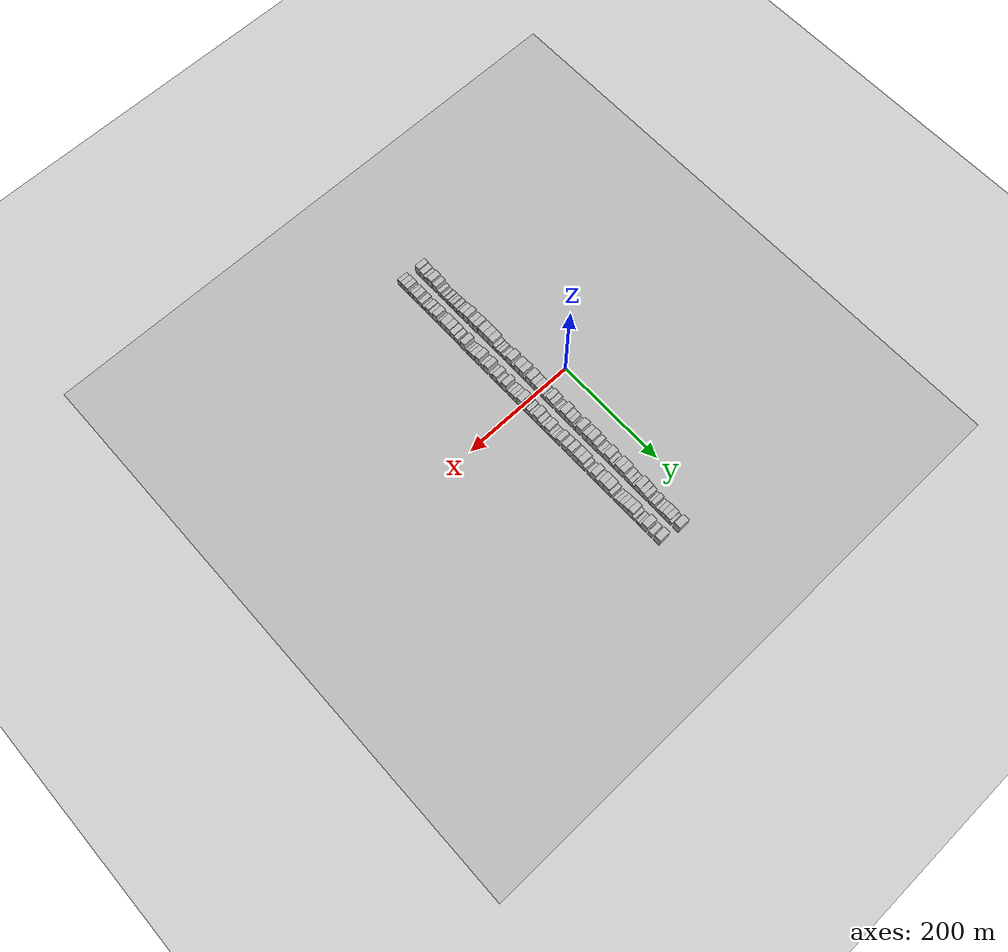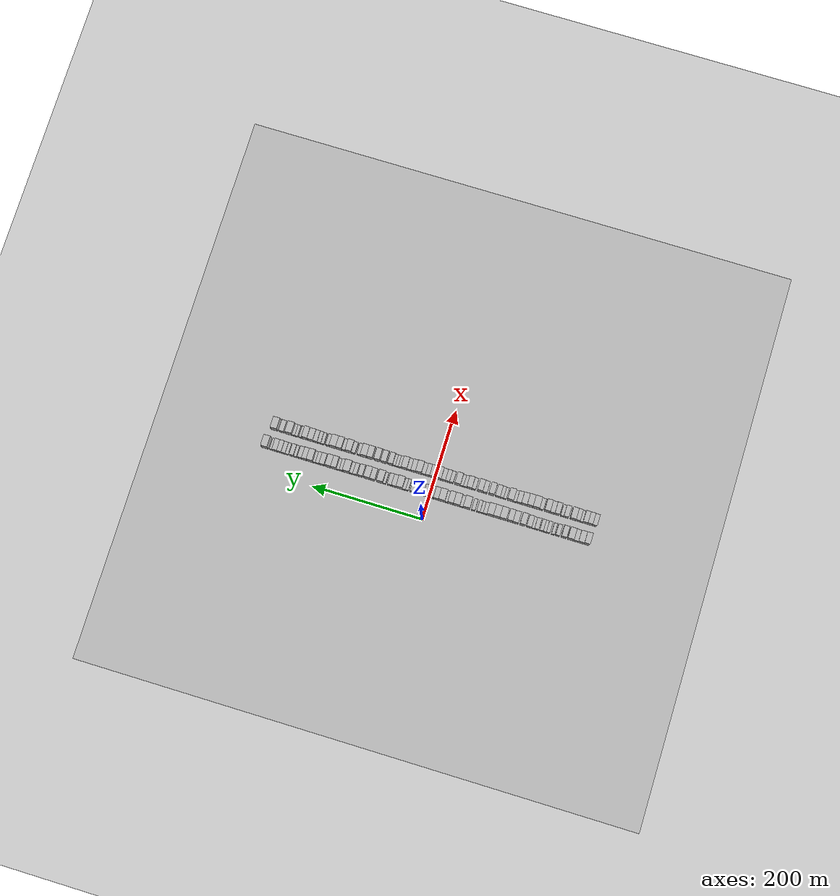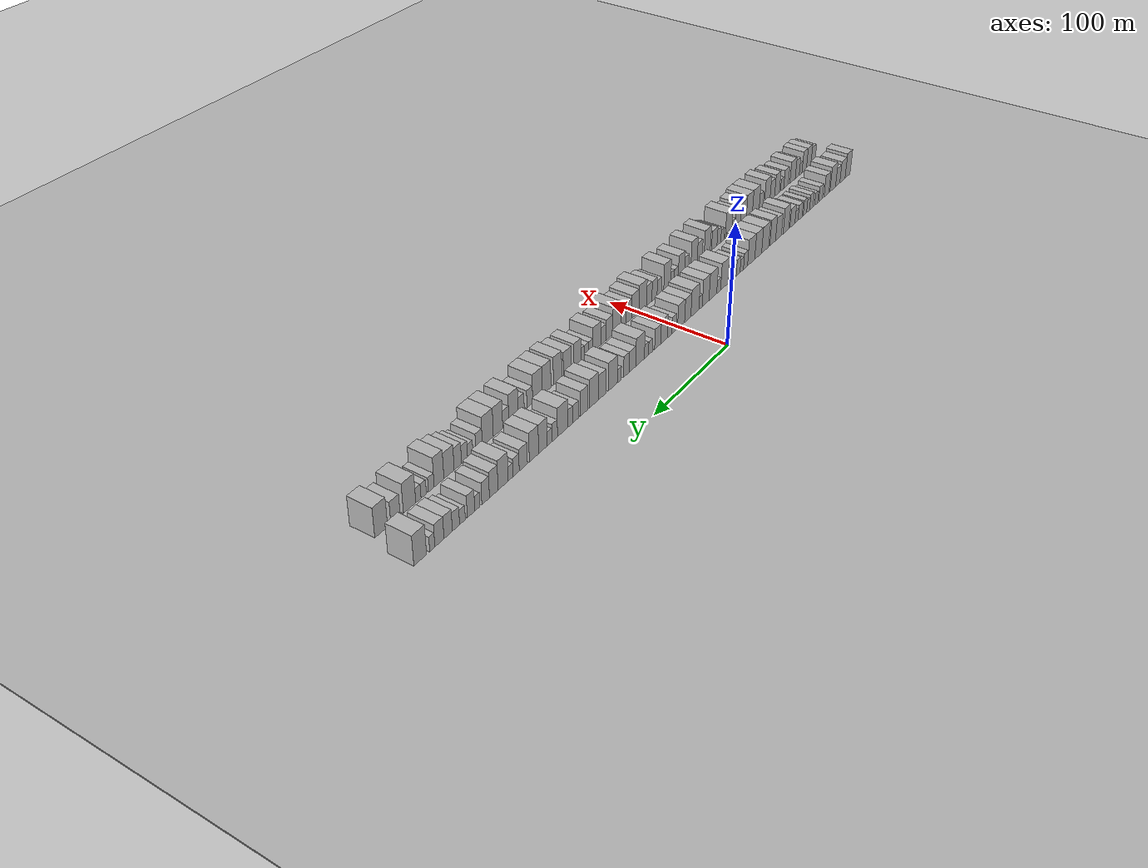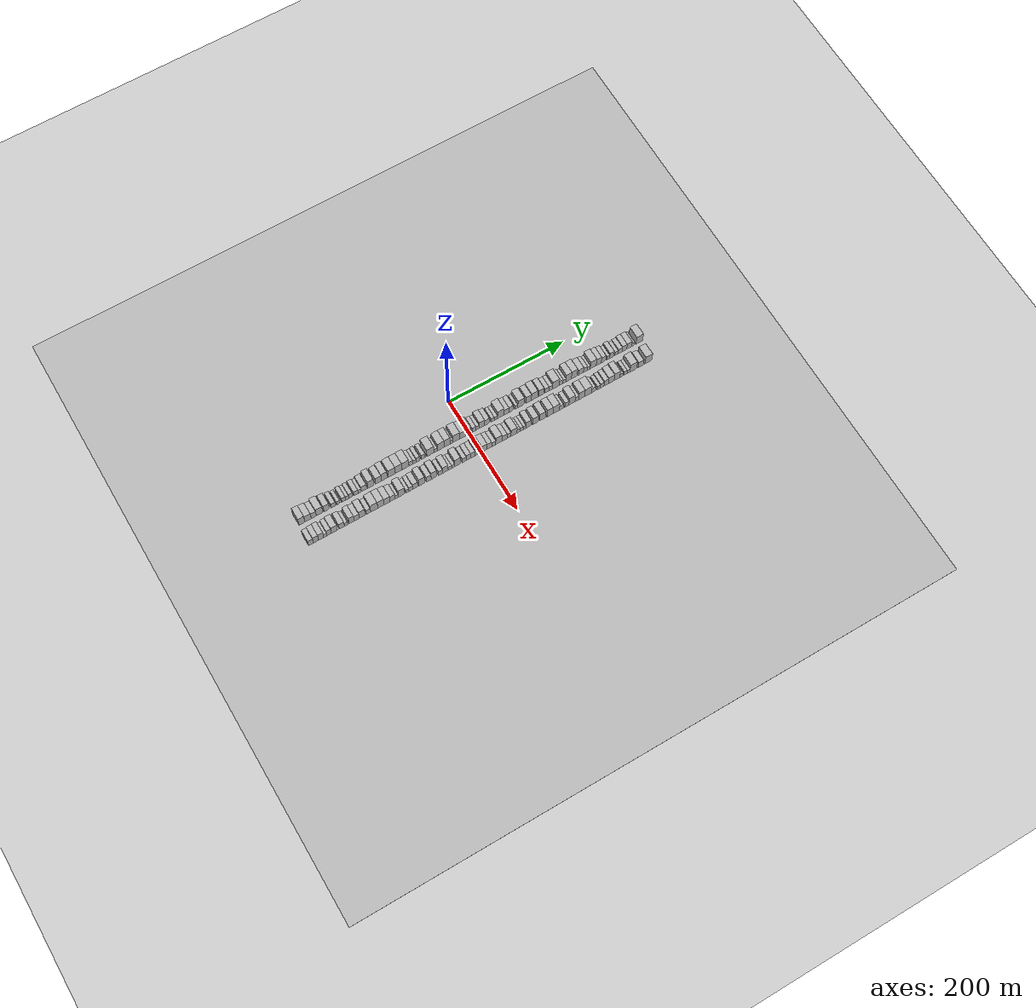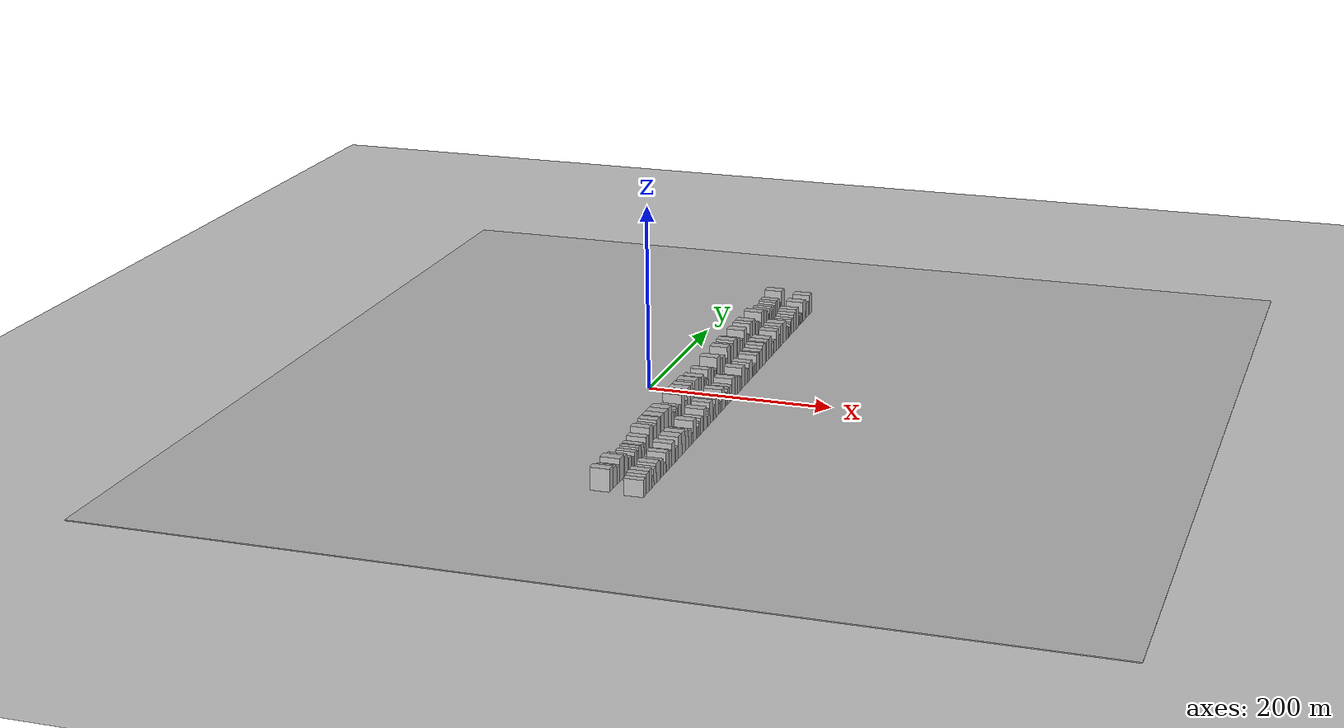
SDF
<?xml version="1.0" encoding="utf-8"?>

<sdf version="1.6">

   <world name="default">

      <gui fullscreen="0">

         <camera name="user_camera">

            <pose>-15 0 4.57585 0 0 0</pose>

            <view_controller>orbit</view_controller>

         </camera>

      </gui>

      <scene>

         <sky>

           <clouds>

             <speed>12</speed>

           </clouds>

         </sky>

         <ambient>0.4 0.4 0.4 1</ambient>

         <background>0.7 0.7 0.7 1</background>

         <shadows>1</shadows>

      </scene>

      <gravity>0 0 -9.8066</gravity>

      <magnetic_field>6e-06 2.3e-05 -4.2e-05</magnetic_field>

      <physics default="0" name="default_physics" type="ode">

         <ode>

            <solver>

               <type>quick</type>

               <iters>10</iters>

               <sor>1.0</sor>

               <use_dynamic_moi_rescaling>0</use_dynamic_moi_rescaling>

            </solver>

            <constraints>

               <cfm>0</cfm>

               <erp>0.2</erp>

               <contact_max_correcting_vel>100</contact_max_correcting_vel>

               <contact_surface_layer>0.001</contact_surface_layer>

            </constraints>

         </ode>

         <max_step_size>0.004</max_step_size>

         <real_time_factor>1</real_time_factor>

         <real_time_update_rate>250</real_time_update_rate>

      </physics>

      <light name="sun" type="directional">

         <cast_shadows>1</cast_shadows>

         <pose>0 0 10 0 0 0</pose>

         <diffuse>0.8 0.8 0.8 1</diffuse>

         <specular>0.2 0.2 0.2 1</specular>

         <attenuation>

            <range>1000</range>

            <constant>0.9</constant>

            <linear>0.01</linear>

            <quadratic>0.001</quadratic>

         </attenuation>

         <direction>-0.5 0.1 -0.9</direction>

      </light>

      <include>

         <name>ground_plane_1</name>

         <uri>model://HANNAS_ground_plane</uri>

         <pose>0 0 0  0 0 0</pose>

      </include>

      <include>

         <name>ground_plane_2</name>

         <uri>model://HANNAS_ground_plane</uri>

         <pose>100 0 0  0 0 0</pose>

      </include>

      <model name="building_1">

         <static>1</static>

         <pose frame="">50.0000 -282.0513 0 0.000000 0.000000 0.000000</pose>

         <link name="link">

            <pose frame="">0 0 12.00 0 0 0</pose>

            <collision name="collision">

               <geometry>

                  <box>

                     <size>20.0000 9.8974 24.0000</size>

                  </box>

               </geometry>

               <max_contacts>10</max_contacts>

               <surface>

                  <contact>

                     <ode/>

                  </contact>

                  <bounce/>

                  <friction>

                     <torsional>

                        <ode/>

                     </torsional>

                     <ode/>

                  </friction>

               </surface>

            </collision>

            <visual name="visual">

               <cast_shadows>0</cast_shadows>

               <geometry>

                  <box>

                     <size>20.0000 9.8974 24.0000</size>

                  </box>

               </geometry>

               <material>

                  <script>

                     <uri>model://HANNAS_wall/materials/scripts</uri>

                     <uri>model://HANNAS_wall/materials/textures</uri>

                     <name>vrc/HANNAS_wall</name>

                  </script>

               </material>

            </visual>

            <self_collide>0</self_collide>

            <enable_wind>0</enable_wind>

            <kinematic>0</kinematic>

         </link>

      </model>

      <model name="building_2">

         <static>1</static>

         <pose frame="">50.0000 -271.9613 0 0.000000 0.000000 0.000000</pose>

         <link name="link">

            <pose frame="">0 0 10.50 0 0 0</pose>

            <collision name="collision">

               <geometry>

                  <box>

                     <size>20.0000 10.2826 21.0000</size>

                  </box>

               </geometry>

               <max_contacts>10</max_contacts>

               <surface>

                  <contact>

                     <ode/>

                  </contact>

                  <bounce/>

                  <friction>

                     <torsional>

                        <ode/>

                     </torsional>

                     <ode/>

                  </friction>

               </surface>

            </collision>

            <visual name="visual">

               <cast_shadows>0</cast_shadows>

               <geometry>

                  <box>

                     <size>20.0000 10.2826 21.0000</size>

                  </box>

               </geometry>

               <material>

                  <script>

                     <uri>model://HANNAS_wall/materials/scripts</uri>

                     <uri>model://HANNAS_wall/materials/textures</uri>

                     <name>vrc/HANNAS_wall</name>

                  </script>

               </material>

            </visual>

            <self_collide>0</self_collide>

            <enable_wind>0</enable_wind>

            <kinematic>0</kinematic>

         </link>

      </model>

      <model name="building_3">

         <static>1</static>

         <pose frame="">50.0000 -262.6088 0 0.000000 0.000000 0.000000</pose>

         <link name="link">

            <pose frame="">0 0 9.00 0 0 0</pose>

            <collision name="collision">

               <geometry>

                  <box>

                     <size>20.0000 8.4224 18.0000</size>

                  </box>

               </geometry>

               <max_contacts>10</max_contacts>

               <surface>

                  <contact>

                     <ode/>

                  </contact>

                  <bounce/>

                  <friction>

                     <torsional>

                        <ode/>

                     </torsional>

                     <ode/>

                  </friction>

               </surface>

            </collision>

            <visual name="visual">

               <cast_shadows>0</cast_shadows>

               <geometry>

                  <box>

                     <size>20.0000 8.4224 18.0000</size>

                  </box>

               </geometry>

               <material>

                  <script>

                     <uri>model://HANNAS_wall/materials/scripts</uri>

                     <uri>model://HANNAS_wall/materials/textures</uri>

                     <name>vrc/HANNAS_wall</name>

                  </script>

               </material>

            </visual>

            <self_collide>0</self_collide>

            <enable_wind>0</enable_wind>

            <kinematic>0</kinematic>

         </link>

      </model>

      <model name="building_4">

         <static>1</static>

         <pose frame="">50.0000 -253.0250 0 0.000000 0.000000 0.000000</pose>

         <link name="link">

            <pose frame="">0 0 12.00 0 0 0</pose>

            <collision name="collision">

               <geometry>

                  <box>

                     <size>20.0000 10.7451 24.0000</size>

                  </box>

               </geometry>

               <max_contacts>10</max_contacts>

               <surface>

                  <contact>

                     <ode/>

                  </contact>

                  <bounce/>

                  <friction>

                     <torsional>

                        <ode/>

                     </torsional>

                     <ode/>

                  </friction>

               </surface>

            </collision>

            <visual name="visual">

               <cast_shadows>0</cast_shadows>

               <geometry>

                  <box>

                     <size>20.0000 10.7451 24.0000</size>

                  </box>

               </geometry>

               <material>

                  <script>

                     <uri>model://HANNAS_wall/materials/scripts</uri>

                     <uri>model://HANNAS_wall/materials/textures</uri>

                     <name>vrc/HANNAS_wall</name>

                  </script>

               </material>

            </visual>

            <self_collide>0</self_collide>

            <enable_wind>0</enable_wind>

            <kinematic>0</kinematic>

         </link>

      </model>

      <model name="building_5">

         <static>1</static>

         <pose frame="">50.0000 -241.0742 0 0.000000 0.000000 0.000000</pose>

         <link name="link">

            <pose frame="">0 0 10.50 0 0 0</pose>

            <collision name="collision">

               <geometry>

                  <box>

                     <size>20.0000 9.1565 21.0000</size>

                  </box>

               </geometry>

               <max_contacts>10</max_contacts>

               <surface>

                  <contact>

                     <ode/>

                  </contact>

                  <bounce/>

                  <friction>

                     <torsional>

                        <ode/>

                     </torsional>

                     <ode/>

                  </friction>

               </surface>

            </collision>

            <visual name="visual">

               <cast_shadows>0</cast_shadows>

               <geometry>

                  <box>

                     <size>20.0000 9.1565 21.0000</size>

                  </box>

               </geometry>

               <material>

                  <script>

                     <uri>model://HANNAS_wall/materials/scripts</uri>

                     <uri>model://HANNAS_wall/materials/textures</uri>

                     <name>vrc/HANNAS_wall</name>

                  </script>

               </material>

            </visual>

            <self_collide>0</self_collide>

            <enable_wind>0</enable_wind>

            <kinematic>0</kinematic>

         </link>

      </model>

      <model name="building_6">

         <static>1</static>

         <pose frame="">50.0000 -229.9674 0 0.000000 0.000000 0.000000</pose>

         <link name="link">

            <pose frame="">0 0 7.50 0 0 0</pose>

            <collision name="collision">

               <geometry>

                  <box>

                     <size>20.0000 7.0570 15.0000</size>

                  </box>

               </geometry>

               <max_contacts>10</max_contacts>

               <surface>

                  <contact>

                     <ode/>

                  </contact>

                  <bounce/>

                  <friction>

                     <torsional>

                        <ode/>

                     </torsional>

                     <ode/>

                  </friction>

               </surface>

            </collision>

            <visual name="visual">

               <cast_shadows>0</cast_shadows>

               <geometry>

                  <box>

                     <size>20.0000 7.0570 15.0000</size>

                  </box>

               </geometry>

               <material>

                  <script>

                     <uri>model://HANNAS_wall/materials/scripts</uri>

                     <uri>model://HANNAS_wall/materials/textures</uri>

                     <name>vrc/HANNAS_wall</name>

                  </script>

               </material>

            </visual>

            <self_collide>0</self_collide>

            <enable_wind>0</enable_wind>

            <kinematic>0</kinematic>

         </link>

      </model>

      <model name="building_7">

         <static>1</static>

         <pose frame="">50.0000 -221.7282 0 0.000000 0.000000 0.000000</pose>

         <link name="link">

            <pose frame="">0 0 6.00 0 0 0</pose>

            <collision name="collision">

               <geometry>

                  <box>

                     <size>20.0000 5.4213 12.0000</size>

                  </box>

               </geometry>

               <max_contacts>10</max_contacts>

               <surface>

                  <contact>

                     <ode/>

                  </contact>

                  <bounce/>

                  <friction>

                     <torsional>

                        <ode/>

                     </torsional>

                     <ode/>

                  </friction>

               </surface>

            </collision>

            <visual name="visual">

               <cast_shadows>0</cast_shadows>

               <geometry>

                  <box>

                     <size>20.0000 5.4213 12.0000</size>

                  </box>

               </geometry>

               <material>

                  <script>

                     <uri>model://HANNAS_wall/materials/scripts</uri>

                     <uri>model://HANNAS_wall/materials/textures</uri>

                     <name>vrc/HANNAS_wall</name>

                  </script>

               </material>

            </visual>

            <self_collide>0</self_collide>

            <enable_wind>0</enable_wind>

            <kinematic>0</kinematic>

         </link>

      </model>

      <model name="building_8">

         <static>1</static>

         <pose frame="">50.0000 -212.8251 0 0.000000 0.000000 0.000000</pose>

         <link name="link">

            <pose frame="">0 0 7.50 0 0 0</pose>

            <collision name="collision">

               <geometry>

                  <box>

                     <size>20.0000 6.3849 15.0000</size>

                  </box>

               </geometry>

               <max_contacts>10</max_contacts>

               <surface>

                  <contact>

                     <ode/>

                  </contact>

                  <bounce/>

                  <friction>

                     <torsional>

                        <ode/>

                     </torsional>

                     <ode/>

                  </friction>

               </surface>

            </collision>

            <visual name="visual">

               <cast_shadows>0</cast_shadows>

               <geometry>

                  <box>

                     <size>20.0000 6.3849 15.0000</size>

                  </box>

               </geometry>

               <material>

                  <script>

                     <uri>model://HANNAS_wall/materials/scripts</uri>

                     <uri>model://HANNAS_wall/materials/textures</uri>

                     <name>vrc/HANNAS_wall</name>

                  </script>

               </material>

            </visual>

            <self_collide>0</self_collide>

            <enable_wind>0</enable_wind>

            <kinematic>0</kinematic>

         </link>

      </model>

      <model name="building_9">

         <static>1</static>

         <pose frame="">50.0000 -206.9112 0 0.000000 0.000000 0.000000</pose>

         <link name="link">

            <pose frame="">0 0 6.00 0 0 0</pose>

            <collision name="collision">

               <geometry>

                  <box>

                     <size>20.0000 5.4429 12.0000</size>

                  </box>

               </geometry>

               <max_contacts>10</max_contacts>

               <surface>

                  <contact>

                     <ode/>

                  </contact>

                  <bounce/>

                  <friction>

                     <torsional>

                        <ode/>

                     </torsional>

                     <ode/>

                  </friction>

               </surface>

            </collision>

            <visual name="visual">

               <cast_shadows>0</cast_shadows>

               <geometry>

                  <box>

                     <size>20.0000 5.4429 12.0000</size>

                  </box>

               </geometry>

               <material>

                  <script>

                     <uri>model://HANNAS_wall/materials/scripts</uri>

                     <uri>model://HANNAS_wall/materials/textures</uri>

                     <name>vrc/HANNAS_wall</name>

                  </script>

               </material>

            </visual>

            <self_collide>0</self_collide>

            <enable_wind>0</enable_wind>

            <kinematic>0</kinematic>

         </link>

      </model>

      <model name="building_10">

         <static>1</static>

         <pose frame="">50.0000 -201.0819 0 0.000000 0.000000 0.000000</pose>

         <link name="link">

            <pose frame="">0 0 7.50 0 0 0</pose>

            <collision name="collision">

               <geometry>

                  <box>

                     <size>20.0000 6.2157 15.0000</size>

                  </box>

               </geometry>

               <max_contacts>10</max_contacts>

               <surface>

                  <contact>

                     <ode/>

                  </contact>

                  <bounce/>

                  <friction>

                     <torsional>

                        <ode/>

                     </torsional>

                     <ode/>

                  </friction>

               </surface>

            </collision>

            <visual name="visual">

               <cast_shadows>0</cast_shadows>

               <geometry>

                  <box>

                     <size>20.0000 6.2157 15.0000</size>

                  </box>

               </geometry>

               <material>

                  <script>

                     <uri>model://HANNAS_wall/materials/scripts</uri>

                     <uri>model://HANNAS_wall/materials/textures</uri>

                     <name>vrc/HANNAS_wall</name>

                  </script>

               </material>

            </visual>

            <self_collide>0</self_collide>

            <enable_wind>0</enable_wind>

            <kinematic>0</kinematic>

         </link>

      </model>

      <model name="building_11">

         <static>1</static>

         <pose frame="">50.0000 -192.2914 0 0.000000 0.000000 0.000000</pose>

         <link name="link">

            <pose frame="">0 0 7.50 0 0 0</pose>

            <collision name="collision">

               <geometry>

                  <box>

                     <size>20.0000 7.3651 15.0000</size>

                  </box>

               </geometry>

               <max_contacts>10</max_contacts>

               <surface>

                  <contact>

                     <ode/>

                  </contact>

                  <bounce/>

                  <friction>

                     <torsional>

                        <ode/>

                     </torsional>

                     <ode/>

                  </friction>

               </surface>

            </collision>

            <visual name="visual">

               <cast_shadows>0</cast_shadows>

               <geometry>

                  <box>

                     <size>20.0000 7.3651 15.0000</size>

                  </box>

               </geometry>

               <material>

                  <script>

                     <uri>model://HANNAS_wall/materials/scripts</uri>

                     <uri>model://HANNAS_wall/materials/textures</uri>

                     <name>vrc/HANNAS_wall</name>

                  </script>

               </material>

            </visual>

            <self_collide>0</self_collide>

            <enable_wind>0</enable_wind>

            <kinematic>0</kinematic>

         </link>

      </model>

      <model name="building_12">

         <static>1</static>

         <pose frame="">50.0000 -185.9395 0 0.000000 0.000000 0.000000</pose>

         <link name="link">

            <pose frame="">0 0 6.00 0 0 0</pose>

            <collision name="collision">

               <geometry>

                  <box>

                     <size>20.0000 5.3388 12.0000</size>

                  </box>

               </geometry>

               <max_contacts>10</max_contacts>

               <surface>

                  <contact>

                     <ode/>

                  </contact>

                  <bounce/>

                  <friction>

                     <torsional>

                        <ode/>

                     </torsional>

                     <ode/>

                  </friction>

               </surface>

            </collision>

            <visual name="visual">

               <cast_shadows>0</cast_shadows>

               <geometry>

                  <box>

                     <size>20.0000 5.3388 12.0000</size>

                  </box>

               </geometry>

               <material>

                  <script>

                     <uri>model://HANNAS_wall/materials/scripts</uri>

                     <uri>model://HANNAS_wall/materials/textures</uri>

                     <name>vrc/HANNAS_wall</name>

                  </script>

               </material>

            </visual>

            <self_collide>0</self_collide>

            <enable_wind>0</enable_wind>

            <kinematic>0</kinematic>

         </link>

      </model>

      <model name="building_13">

         <static>1</static>

         <pose frame="">50.0000 -178.7974 0 0.000000 0.000000 0.000000</pose>

         <link name="link">

            <pose frame="">0 0 9.00 0 0 0</pose>

            <collision name="collision">

               <geometry>

                  <box>

                     <size>20.0000 8.9453 18.0000</size>

                  </box>

               </geometry>

               <max_contacts>10</max_contacts>

               <surface>

                  <contact>

                     <ode/>

                  </contact>

                  <bounce/>

                  <friction>

                     <torsional>

                        <ode/>

                     </torsional>

                     <ode/>

                  </friction>

               </surface>

            </collision>

            <visual name="visual">

               <cast_shadows>0</cast_shadows>

               <geometry>

                  <box>

                     <size>20.0000 8.9453 18.0000</size>

                  </box>

               </geometry>

               <material>

                  <script>

                     <uri>model://HANNAS_wall/materials/scripts</uri>

                     <uri>model://HANNAS_wall/materials/textures</uri>

                     <name>vrc/HANNAS_wall</name>

                  </script>

               </material>

            </visual>

            <self_collide>0</self_collide>

            <enable_wind>0</enable_wind>

            <kinematic>0</kinematic>

         </link>

      </model>

      <model name="building_14">

         <static>1</static>

         <pose frame="">50.0000 -167.3795 0 0.000000 0.000000 0.000000</pose>

         <link name="link">

            <pose frame="">0 0 12.00 0 0 0</pose>

            <collision name="collision">

               <geometry>

                  <box>

                     <size>20.0000 9.8905 24.0000</size>

                  </box>

               </geometry>

               <max_contacts>10</max_contacts>

               <surface>

                  <contact>

                     <ode/>

                  </contact>

                  <bounce/>

                  <friction>

                     <torsional>

                        <ode/>

                     </torsional>

                     <ode/>

                  </friction>

               </surface>

            </collision>

            <visual name="visual">

               <cast_shadows>0</cast_shadows>

               <geometry>

                  <box>

                     <size>20.0000 9.8905 24.0000</size>

                  </box>

               </geometry>

               <material>

                  <script>

                     <uri>model://HANNAS_wall/materials/scripts</uri>

                     <uri>model://HANNAS_wall/materials/textures</uri>

                     <name>vrc/HANNAS_wall</name>

                  </script>

               </material>

            </visual>

            <self_collide>0</self_collide>

            <enable_wind>0</enable_wind>

            <kinematic>0</kinematic>

         </link>

      </model>

      <model name="building_15">

         <static>1</static>

         <pose frame="">50.0000 -154.4756 0 0.000000 0.000000 0.000000</pose>

         <link name="link">

            <pose frame="">0 0 10.50 0 0 0</pose>

            <collision name="collision">

               <geometry>

                  <box>

                     <size>20.0000 9.9173 21.0000</size>

                  </box>

               </geometry>

               <max_contacts>10</max_contacts>

               <surface>

                  <contact>

                     <ode/>

                  </contact>

                  <bounce/>

                  <friction>

                     <torsional>

                        <ode/>

                     </torsional>

                     <ode/>

                  </friction>

               </surface>

            </collision>

            <visual name="visual">

               <cast_shadows>0</cast_shadows>

               <geometry>

                  <box>

                     <size>20.0000 9.9173 21.0000</size>

                  </box>

               </geometry>

               <material>

                  <script>

                     <uri>model://HANNAS_wall/materials/scripts</uri>

                     <uri>model://HANNAS_wall/materials/textures</uri>

                     <name>vrc/HANNAS_wall</name>

                  </script>

               </material>

            </visual>

            <self_collide>0</self_collide>

            <enable_wind>0</enable_wind>

            <kinematic>0</kinematic>

         </link>

      </model>

      <model name="building_16">

         <static>1</static>

         <pose frame="">50.0000 -144.6317 0 0.000000 0.000000 0.000000</pose>

         <link name="link">

            <pose frame="">0 0 12.00 0 0 0</pose>

            <collision name="collision">

               <geometry>

                  <box>

                     <size>20.0000 9.7707 24.0000</size>

                  </box>

               </geometry>

               <max_contacts>10</max_contacts>

               <surface>

                  <contact>

                     <ode/>

                  </contact>

                  <bounce/>

                  <friction>

                     <torsional>

                        <ode/>

                     </torsional>

                     <ode/>

                  </friction>

               </surface>

            </collision>

            <visual name="visual">

               <cast_shadows>0</cast_shadows>

               <geometry>

                  <box>

                     <size>20.0000 9.7707 24.0000</size>

                  </box>

               </geometry>

               <material>

                  <script>

                     <uri>model://HANNAS_wall/materials/scripts</uri>

                     <uri>model://HANNAS_wall/materials/textures</uri>

                     <name>vrc/HANNAS_wall</name>

                  </script>

               </material>

            </visual>

            <self_collide>0</self_collide>

            <enable_wind>0</enable_wind>

            <kinematic>0</kinematic>

         </link>

      </model>

      <model name="building_17">

         <static>1</static>

         <pose frame="">50.0000 -131.8919 0 0.000000 0.000000 0.000000</pose>

         <link name="link">

            <pose frame="">0 0 12.00 0 0 0</pose>

            <collision name="collision">

               <geometry>

                  <box>

                     <size>20.0000 11.7087 24.0000</size>

                  </box>

               </geometry>

               <max_contacts>10</max_contacts>

               <surface>

                  <contact>

                     <ode/>

                  </contact>

                  <bounce/>

                  <friction>

                     <torsional>

                        <ode/>

                     </torsional>

                     <ode/>

                  </friction>

               </surface>

            </collision>

            <visual name="visual">

               <cast_shadows>0</cast_shadows>

               <geometry>

                  <box>

                     <size>20.0000 11.7087 24.0000</size>

                  </box>

               </geometry>

               <material>

                  <script>

                     <uri>model://HANNAS_wall/materials/scripts</uri>

                     <uri>model://HANNAS_wall/materials/textures</uri>

                     <name>vrc/HANNAS_wall</name>

                  </script>

               </material>

            </visual>

            <self_collide>0</self_collide>

            <enable_wind>0</enable_wind>

            <kinematic>0</kinematic>

         </link>

      </model>

      <model name="building_18">

         <static>1</static>

         <pose frame="">50.0000 -120.3263 0 0.000000 0.000000 0.000000</pose>

         <link name="link">

            <pose frame="">0 0 12.00 0 0 0</pose>

            <collision name="collision">

               <geometry>

                  <box>

                     <size>20.0000 11.4226 24.0000</size>

                  </box>

               </geometry>

               <max_contacts>10</max_contacts>

               <surface>

                  <contact>

                     <ode/>

                  </contact>

                  <bounce/>

                  <friction>

                     <torsional>

                        <ode/>

                     </torsional>

                     <ode/>

                  </friction>

               </surface>

            </collision>

            <visual name="visual">

               <cast_shadows>0</cast_shadows>

               <geometry>

                  <box>

                     <size>20.0000 11.4226 24.0000</size>

                  </box>

               </geometry>

               <material>

                  <script>

                     <uri>model://HANNAS_wall/materials/scripts</uri>

                     <uri>model://HANNAS_wall/materials/textures</uri>

                     <name>vrc/HANNAS_wall</name>

                  </script>

               </material>

            </visual>

            <self_collide>0</self_collide>

            <enable_wind>0</enable_wind>

            <kinematic>0</kinematic>

         </link>

      </model>

      <model name="building_19">

         <static>1</static>

         <pose frame="">50.0000 -108.8192 0 0.000000 0.000000 0.000000</pose>

         <link name="link">

            <pose frame="">0 0 12.00 0 0 0</pose>

            <collision name="collision">

               <geometry>

                  <box>

                     <size>20.0000 11.5916 24.0000</size>

                  </box>

               </geometry>

               <max_contacts>10</max_contacts>

               <surface>

                  <contact>

                     <ode/>

                  </contact>

                  <bounce/>

                  <friction>

                     <torsional>

                        <ode/>

                     </torsional>

                     <ode/>

                  </friction>

               </surface>

            </collision>

            <visual name="visual">

               <cast_shadows>0</cast_shadows>

               <geometry>

                  <box>

                     <size>20.0000 11.5916 24.0000</size>

                  </box>

               </geometry>

               <material>

                  <script>

                     <uri>model://HANNAS_wall/materials/scripts</uri>

                     <uri>model://HANNAS_wall/materials/textures</uri>

                     <name>vrc/HANNAS_wall</name>

                  </script>

               </material>

            </visual>

            <self_collide>0</self_collide>

            <enable_wind>0</enable_wind>

            <kinematic>0</kinematic>

         </link>

      </model>

      <model name="building_20">

         <static>1</static>

         <pose frame="">50.0000 -99.7000 0 0.000000 0.000000 0.000000</pose>

         <link name="link">

            <pose frame="">0 0 7.50 0 0 0</pose>

            <collision name="collision">

               <geometry>

                  <box>

                     <size>20.0000 6.6468 15.0000</size>

                  </box>

               </geometry>

               <max_contacts>10</max_contacts>

               <surface>

                  <contact>

                     <ode/>

                  </contact>

                  <bounce/>

                  <friction>

                     <torsional>

                        <ode/>

                     </torsional>

                     <ode/>

                  </friction>

               </surface>

            </collision>

            <visual name="visual">

               <cast_shadows>0</cast_shadows>

               <geometry>

                  <box>

                     <size>20.0000 6.6468 15.0000</size>

                  </box>

               </geometry>

               <material>

                  <script>

                     <uri>model://HANNAS_wall/materials/scripts</uri>

                     <uri>model://HANNAS_wall/materials/textures</uri>

                     <name>vrc/HANNAS_wall</name>

                  </script>

               </material>

            </visual>

            <self_collide>0</self_collide>

            <enable_wind>0</enable_wind>

            <kinematic>0</kinematic>

         </link>

      </model>

      <model name="building_21">

         <static>1</static>

         <pose frame="">50.0000 -93.6242 0 0.000000 0.000000 0.000000</pose>

         <link name="link">

            <pose frame="">0 0 6.00 0 0 0</pose>

            <collision name="collision">

               <geometry>

                  <box>

                     <size>20.0000 5.5048 12.0000</size>

                  </box>

               </geometry>

               <max_contacts>10</max_contacts>

               <surface>

                  <contact>

                     <ode/>

                  </contact>

                  <bounce/>

                  <friction>

                     <torsional>

                        <ode/>

                     </torsional>

                     <ode/>

                  </friction>

               </surface>

            </collision>

            <visual name="visual">

               <cast_shadows>0</cast_shadows>

               <geometry>

                  <box>

                     <size>20.0000 5.5048 12.0000</size>

                  </box>

               </geometry>

               <material>

                  <script>

                     <uri>model://HANNAS_wall/materials/scripts</uri>

                     <uri>model://HANNAS_wall/materials/textures</uri>

                     <name>vrc/HANNAS_wall</name>

                  </script>

               </material>

            </visual>

            <self_collide>0</self_collide>

            <enable_wind>0</enable_wind>

            <kinematic>0</kinematic>

         </link>

      </model>

      <model name="building_22">

         <static>1</static>

         <pose frame="">50.0000 -87.8375 0 0.000000 0.000000 0.000000</pose>

         <link name="link">

            <pose frame="">0 0 7.50 0 0 0</pose>

            <collision name="collision">

               <geometry>

                  <box>

                     <size>20.0000 6.0685 15.0000</size>

                  </box>

               </geometry>

               <max_contacts>10</max_contacts>

               <surface>

                  <contact>

                     <ode/>

                  </contact>

                  <bounce/>

                  <friction>

                     <torsional>

                        <ode/>

                     </torsional>

                     <ode/>

                  </friction>

               </surface>

            </collision>

            <visual name="visual">

               <cast_shadows>0</cast_shadows>

               <geometry>

                  <box>

                     <size>20.0000 6.0685 15.0000</size>

                  </box>

               </geometry>

               <material>

                  <script>

                     <uri>model://HANNAS_wall/materials/scripts</uri>

                     <uri>model://HANNAS_wall/materials/textures</uri>

                     <name>vrc/HANNAS_wall</name>

                  </script>

               </material>

            </visual>

            <self_collide>0</self_collide>

            <enable_wind>0</enable_wind>

            <kinematic>0</kinematic>

         </link>

      </model>

      <model name="building_23">

         <static>1</static>

         <pose frame="">50.0000 -78.6483 0 0.000000 0.000000 0.000000</pose>

         <link name="link">

            <pose frame="">0 0 7.50 0 0 0</pose>

            <collision name="collision">

               <geometry>

                  <box>

                     <size>20.0000 6.3099 15.0000</size>

                  </box>

               </geometry>

               <max_contacts>10</max_contacts>

               <surface>

                  <contact>

                     <ode/>

                  </contact>

                  <bounce/>

                  <friction>

                     <torsional>

                        <ode/>

                     </torsional>

                     <ode/>

                  </friction>

               </surface>

            </collision>

            <visual name="visual">

               <cast_shadows>0</cast_shadows>

               <geometry>

                  <box>

                     <size>20.0000 6.3099 15.0000</size>

                  </box>

               </geometry>

               <material>

                  <script>

                     <uri>model://HANNAS_wall/materials/scripts</uri>

                     <uri>model://HANNAS_wall/materials/textures</uri>

                     <name>vrc/HANNAS_wall</name>

                  </script>

               </material>

            </visual>

            <self_collide>0</self_collide>

            <enable_wind>0</enable_wind>

            <kinematic>0</kinematic>

         </link>

      </model>

      <model name="building_24">

         <static>1</static>

         <pose frame="">50.0000 -66.4963 0 0.000000 0.000000 0.000000</pose>

         <link name="link">

            <pose frame="">0 0 12.00 0 0 0</pose>

            <collision name="collision">

               <geometry>

                  <box>

                     <size>20.0000 11.9940 24.0000</size>

                  </box>

               </geometry>

               <max_contacts>10</max_contacts>

               <surface>

                  <contact>

                     <ode/>

                  </contact>

                  <bounce/>

                  <friction>

                     <torsional>

                        <ode/>

                     </torsional>

                     <ode/>

                  </friction>

               </surface>

            </collision>

            <visual name="visual">

               <cast_shadows>0</cast_shadows>

               <geometry>

                  <box>

                     <size>20.0000 11.9940 24.0000</size>

                  </box>

               </geometry>

               <material>

                  <script>

                     <uri>model://HANNAS_wall/materials/scripts</uri>

                     <uri>model://HANNAS_wall/materials/textures</uri>

                     <name>vrc/HANNAS_wall</name>

                  </script>

               </material>

            </visual>

            <self_collide>0</self_collide>

            <enable_wind>0</enable_wind>

            <kinematic>0</kinematic>

         </link>

      </model>

      <model name="building_25">

         <static>1</static>

         <pose frame="">50.0000 -57.5292 0 0.000000 0.000000 0.000000</pose>

         <link name="link">

            <pose frame="">0 0 6.00 0 0 0</pose>

            <collision name="collision">

               <geometry>

                  <box>

                     <size>20.0000 5.9402 12.0000</size>

                  </box>

               </geometry>

               <max_contacts>10</max_contacts>

               <surface>

                  <contact>

                     <ode/>

                  </contact>

                  <bounce/>

                  <friction>

                     <torsional>

                        <ode/>

                     </torsional>

                     <ode/>

                  </friction>

               </surface>

            </collision>

            <visual name="visual">

               <cast_shadows>0</cast_shadows>

               <geometry>

                  <box>

                     <size>20.0000 5.9402 12.0000</size>

                  </box>

               </geometry>

               <material>

                  <script>

                     <uri>model://HANNAS_wall/materials/scripts</uri>

                     <uri>model://HANNAS_wall/materials/textures</uri>

                     <name>vrc/HANNAS_wall</name>

                  </script>

               </material>

            </visual>

            <self_collide>0</self_collide>

            <enable_wind>0</enable_wind>

            <kinematic>0</kinematic>

         </link>

      </model>

      <model name="building_26">

         <static>1</static>

         <pose frame="">50.0000 -48.7081 0 0.000000 0.000000 0.000000</pose>

         <link name="link">

            <pose frame="">0 0 12.00 0 0 0</pose>

            <collision name="collision">

               <geometry>

                  <box>

                     <size>20.0000 11.7020 24.0000</size>

                  </box>

               </geometry>

               <max_contacts>10</max_contacts>

               <surface>

                  <contact>

                     <ode/>

                  </contact>

                  <bounce/>

                  <friction>

                     <torsional>

                        <ode/>

                     </torsional>

                     <ode/>

                  </friction>

               </surface>

            </collision>

            <visual name="visual">

               <cast_shadows>0</cast_shadows>

               <geometry>

                  <box>

                     <size>20.0000 11.7020 24.0000</size>

                  </box>

               </geometry>

               <material>

                  <script>

                     <uri>model://HANNAS_wall/materials/scripts</uri>

                     <uri>model://HANNAS_wall/materials/textures</uri>

                     <name>vrc/HANNAS_wall</name>

                  </script>

               </material>

            </visual>

            <self_collide>0</self_collide>

            <enable_wind>0</enable_wind>

            <kinematic>0</kinematic>

         </link>

      </model>

      <model name="building_27">

         <static>1</static>

         <pose frame="">50.0000 -37.8159 0 0.000000 0.000000 0.000000</pose>

         <link name="link">

            <pose frame="">0 0 12.00 0 0 0</pose>

            <collision name="collision">

               <geometry>

                  <box>

                     <size>20.0000 10.0824 24.0000</size>

                  </box>

               </geometry>

               <max_contacts>10</max_contacts>

               <surface>

                  <contact>

                     <ode/>

                  </contact>

                  <bounce/>

                  <friction>

                     <torsional>

                        <ode/>

                     </torsional>

                     <ode/>

                  </friction>

               </surface>

            </collision>

            <visual name="visual">

               <cast_shadows>0</cast_shadows>

               <geometry>

                  <box>

                     <size>20.0000 10.0824 24.0000</size>

                  </box>

               </geometry>

               <material>

                  <script>

                     <uri>model://HANNAS_wall/materials/scripts</uri>

                     <uri>model://HANNAS_wall/materials/textures</uri>

                     <name>vrc/HANNAS_wall</name>

                  </script>

               </material>

            </visual>

            <self_collide>0</self_collide>

            <enable_wind>0</enable_wind>

            <kinematic>0</kinematic>

         </link>

      </model>

      <model name="building_28">

         <static>1</static>

         <pose frame="">50.0000 -30.2963 0 0.000000 0.000000 0.000000</pose>

         <link name="link">

            <pose frame="">0 0 6.00 0 0 0</pose>

            <collision name="collision">

               <geometry>

                  <box>

                     <size>20.0000 4.9567 12.0000</size>

                  </box>

               </geometry>

               <max_contacts>10</max_contacts>

               <surface>

                  <contact>

                     <ode/>

                  </contact>

                  <bounce/>

                  <friction>

                     <torsional>

                        <ode/>

                     </torsional>

                     <ode/>

                  </friction>

               </surface>

            </collision>

            <visual name="visual">

               <cast_shadows>0</cast_shadows>

               <geometry>

                  <box>

                     <size>20.0000 4.9567 12.0000</size>

                  </box>

               </geometry>

               <material>

                  <script>

                     <uri>model://HANNAS_wall/materials/scripts</uri>

                     <uri>model://HANNAS_wall/materials/textures</uri>

                     <name>vrc/HANNAS_wall</name>

                  </script>

               </material>

            </visual>

            <self_collide>0</self_collide>

            <enable_wind>0</enable_wind>

            <kinematic>0</kinematic>

         </link>

      </model>

      <model name="building_29">

         <static>1</static>

         <pose frame="">50.0000 -21.9319 0 0.000000 0.000000 0.000000</pose>

         <link name="link">

            <pose frame="">0 0 12.00 0 0 0</pose>

            <collision name="collision">

               <geometry>

                  <box>

                     <size>20.0000 11.7722 24.0000</size>

                  </box>

               </geometry>

               <max_contacts>10</max_contacts>

               <surface>

                  <contact>

                     <ode/>

                  </contact>

                  <bounce/>

                  <friction>

                     <torsional>

                        <ode/>

                     </torsional>

                     <ode/>

                  </friction>

               </surface>

            </collision>

            <visual name="visual">

               <cast_shadows>0</cast_shadows>

               <geometry>

                  <box>

                     <size>20.0000 11.7722 24.0000</size>

                  </box>

               </geometry>

               <material>

                  <script>

                     <uri>model://HANNAS_wall/materials/scripts</uri>

                     <uri>model://HANNAS_wall/materials/textures</uri>

                     <name>vrc/HANNAS_wall</name>

                  </script>

               </material>

            </visual>

            <self_collide>0</self_collide>

            <enable_wind>0</enable_wind>

            <kinematic>0</kinematic>

         </link>

      </model>

      <model name="building_30">

         <static>1</static>

         <pose frame="">50.0000 -11.4976 0 0.000000 0.000000 0.000000</pose>

         <link name="link">

            <pose frame="">0 0 10.50 0 0 0</pose>

            <collision name="collision">

               <geometry>

                  <box>

                     <size>20.0000 9.0964 21.0000</size>

                  </box>

               </geometry>

               <max_contacts>10</max_contacts>

               <surface>

                  <contact>

                     <ode/>

                  </contact>

                  <bounce/>

                  <friction>

                     <torsional>

                        <ode/>

                     </torsional>

                     <ode/>

                  </friction>

               </surface>

            </collision>

            <visual name="visual">

               <cast_shadows>0</cast_shadows>

               <geometry>

                  <box>

                     <size>20.0000 9.0964 21.0000</size>

                  </box>

               </geometry>

               <material>

                  <script>

                     <uri>model://HANNAS_wall/materials/scripts</uri>

                     <uri>model://HANNAS_wall/materials/textures</uri>

                     <name>vrc/HANNAS_wall</name>

                  </script>

               </material>

            </visual>

            <self_collide>0</self_collide>

            <enable_wind>0</enable_wind>

            <kinematic>0</kinematic>

         </link>

      </model>

      <model name="building_31">

         <static>1</static>

         <pose frame="">50.0000 -1.9482 0 0.000000 0.000000 0.000000</pose>

         <link name="link">

            <pose frame="">0 0 10.50 0 0 0</pose>

            <collision name="collision">

               <geometry>

                  <box>

                     <size>20.0000 10.0025 21.0000</size>

                  </box>

               </geometry>

               <max_contacts>10</max_contacts>

               <surface>

                  <contact>

                     <ode/>

                  </contact>

                  <bounce/>

                  <friction>

                     <torsional>

                        <ode/>

                     </torsional>

                     <ode/>

                  </friction>

               </surface>

            </collision>

            <visual name="visual">

               <cast_shadows>0</cast_shadows>

               <geometry>

                  <box>

                     <size>20.0000 10.0025 21.0000</size>

                  </box>

               </geometry>

               <material>

                  <script>

                     <uri>model://HANNAS_wall/materials/scripts</uri>

                     <uri>model://HANNAS_wall/materials/textures</uri>

                     <name>vrc/HANNAS_wall</name>

                  </script>

               </material>

            </visual>

            <self_collide>0</self_collide>

            <enable_wind>0</enable_wind>

            <kinematic>0</kinematic>

         </link>

      </model>

      <model name="building_32">

         <static>1</static>

         <pose frame="">50.0000 8.2210 0 0.000000 0.000000 0.000000</pose>

         <link name="link">

            <pose frame="">0 0 7.50 0 0 0</pose>

            <collision name="collision">

               <geometry>

                  <box>

                     <size>20.0000 6.3358 15.0000</size>

                  </box>

               </geometry>

               <max_contacts>10</max_contacts>

               <surface>

                  <contact>

                     <ode/>

                  </contact>

                  <bounce/>

                  <friction>

                     <torsional>

                        <ode/>

                     </torsional>

                     <ode/>

                  </friction>

               </surface>

            </collision>

            <visual name="visual">

               <cast_shadows>0</cast_shadows>

               <geometry>

                  <box>

                     <size>20.0000 6.3358 15.0000</size>

                  </box>

               </geometry>

               <material>

                  <script>

                     <uri>model://HANNAS_wall/materials/scripts</uri>

                     <uri>model://HANNAS_wall/materials/textures</uri>

                     <name>vrc/HANNAS_wall</name>

                  </script>

               </material>

            </visual>

            <self_collide>0</self_collide>

            <enable_wind>0</enable_wind>

            <kinematic>0</kinematic>

         </link>

      </model>

      <model name="building_33">

         <static>1</static>

         <pose frame="">50.0000 14.3444 0 0.000000 0.000000 0.000000</pose>

         <link name="link">

            <pose frame="">0 0 6.00 0 0 0</pose>

            <collision name="collision">

               <geometry>

                  <box>

                     <size>20.0000 5.9111 12.0000</size>

                  </box>

               </geometry>

               <max_contacts>10</max_contacts>

               <surface>

                  <contact>

                     <ode/>

                  </contact>

                  <bounce/>

                  <friction>

                     <torsional>

                        <ode/>

                     </torsional>

                     <ode/>

                  </friction>

               </surface>

            </collision>

            <visual name="visual">

               <cast_shadows>0</cast_shadows>

               <geometry>

                  <box>

                     <size>20.0000 5.9111 12.0000</size>

                  </box>

               </geometry>

               <material>

                  <script>

                     <uri>model://HANNAS_wall/materials/scripts</uri>

                     <uri>model://HANNAS_wall/materials/textures</uri>

                     <name>vrc/HANNAS_wall</name>

                  </script>

               </material>

            </visual>

            <self_collide>0</self_collide>

            <enable_wind>0</enable_wind>

            <kinematic>0</kinematic>

         </link>

      </model>

      <model name="building_34">

         <static>1</static>

         <pose frame="">50.0000 21.9652 0 0.000000 0.000000 0.000000</pose>

         <link name="link">

            <pose frame="">0 0 10.50 0 0 0</pose>

            <collision name="collision">

               <geometry>

                  <box>

                     <size>20.0000 9.3304 21.0000</size>

                  </box>

               </geometry>

               <max_contacts>10</max_contacts>

               <surface>

                  <contact>

                     <ode/>

                  </contact>

                  <bounce/>

                  <friction>

                     <torsional>

                        <ode/>

                     </torsional>

                     <ode/>

                  </friction>

               </surface>

            </collision>

            <visual name="visual">

               <cast_shadows>0</cast_shadows>

               <geometry>

                  <box>

                     <size>20.0000 9.3304 21.0000</size>

                  </box>

               </geometry>

               <material>

                  <script>

                     <uri>model://HANNAS_wall/materials/scripts</uri>

                     <uri>model://HANNAS_wall/materials/textures</uri>

                     <name>vrc/HANNAS_wall</name>

                  </script>

               </material>

            </visual>

            <self_collide>0</self_collide>

            <enable_wind>0</enable_wind>

            <kinematic>0</kinematic>

         </link>

      </model>

      <model name="building_35">

         <static>1</static>

         <pose frame="">50.0000 30.7936 0 0.000000 0.000000 0.000000</pose>

         <link name="link">

            <pose frame="">0 0 9.00 0 0 0</pose>

            <collision name="collision">

               <geometry>

                  <box>

                     <size>20.0000 8.3263 18.0000</size>

                  </box>

               </geometry>

               <max_contacts>10</max_contacts>

               <surface>

                  <contact>

                     <ode/>

                  </contact>

                  <bounce/>

                  <friction>

                     <torsional>

                        <ode/>

                     </torsional>

                     <ode/>

                  </friction>

               </surface>

            </collision>

            <visual name="visual">

               <cast_shadows>0</cast_shadows>

               <geometry>

                  <box>

                     <size>20.0000 8.3263 18.0000</size>

                  </box>

               </geometry>

               <material>

                  <script>

                     <uri>model://HANNAS_wall/materials/scripts</uri>

                     <uri>model://HANNAS_wall/materials/textures</uri>

                     <name>vrc/HANNAS_wall</name>

                  </script>

               </material>

            </visual>

            <self_collide>0</self_collide>

            <enable_wind>0</enable_wind>

            <kinematic>0</kinematic>

         </link>

      </model>

      <model name="building_36">

         <static>1</static>

         <pose frame="">50.0000 40.5594 0 0.000000 0.000000 0.000000</pose>

         <link name="link">

            <pose frame="">0 0 6.00 0 0 0</pose>

            <collision name="collision">

               <geometry>

                  <box>

                     <size>20.0000 5.2052 12.0000</size>

                  </box>

               </geometry>

               <max_contacts>10</max_contacts>

               <surface>

                  <contact>

                     <ode/>

                  </contact>

                  <bounce/>

                  <friction>

                     <torsional>

                        <ode/>

                     </torsional>

                     <ode/>

                  </friction>

               </surface>

            </collision>

            <visual name="visual">

               <cast_shadows>0</cast_shadows>

               <geometry>

                  <box>

                     <size>20.0000 5.2052 12.0000</size>

                  </box>

               </geometry>

               <material>

                  <script>

                     <uri>model://HANNAS_wall/materials/scripts</uri>

                     <uri>model://HANNAS_wall/materials/textures</uri>

                     <name>vrc/HANNAS_wall</name>

                  </script>

               </material>

            </visual>

            <self_collide>0</self_collide>

            <enable_wind>0</enable_wind>

            <kinematic>0</kinematic>

         </link>

      </model>

      <model name="building_37">

         <static>1</static>

         <pose frame="">50.0000 45.9524 0 0.000000 0.000000 0.000000</pose>

         <link name="link">

            <pose frame="">0 0 6.00 0 0 0</pose>

            <collision name="collision">

               <geometry>

                  <box>

                     <size>20.0000 5.5808 12.0000</size>

                  </box>

               </geometry>

               <max_contacts>10</max_contacts>

               <surface>

                  <contact>

                     <ode/>

                  </contact>

                  <bounce/>

                  <friction>

                     <torsional>

                        <ode/>

                     </torsional>

                     <ode/>

                  </friction>

               </surface>

            </collision>

            <visual name="visual">

               <cast_shadows>0</cast_shadows>

               <geometry>

                  <box>

                     <size>20.0000 5.5808 12.0000</size>

                  </box>

               </geometry>

               <material>

                  <script>

                     <uri>model://HANNAS_wall/materials/scripts</uri>

                     <uri>model://HANNAS_wall/materials/textures</uri>

                     <name>vrc/HANNAS_wall</name>

                  </script>

               </material>

            </visual>

            <self_collide>0</self_collide>

            <enable_wind>0</enable_wind>

            <kinematic>0</kinematic>

         </link>

      </model>

      <model name="building_38">

         <static>1</static>

         <pose frame="">50.0000 54.4894 0 0.000000 0.000000 0.000000</pose>

         <link name="link">

            <pose frame="">0 0 12.00 0 0 0</pose>

            <collision name="collision">

               <geometry>

                  <box>

                     <size>20.0000 11.4933 24.0000</size>

                  </box>

               </geometry>

               <max_contacts>10</max_contacts>

               <surface>

                  <contact>

                     <ode/>

                  </contact>

                  <bounce/>

                  <friction>

                     <torsional>

                        <ode/>

                     </torsional>

                     <ode/>

                  </friction>

               </surface>

            </collision>

            <visual name="visual">

               <cast_shadows>0</cast_shadows>

               <geometry>

                  <box>

                     <size>20.0000 11.4933 24.0000</size>

                  </box>

               </geometry>

               <material>

                  <script>

                     <uri>model://HANNAS_wall/materials/scripts</uri>

                     <uri>model://HANNAS_wall/materials/textures</uri>

                     <name>vrc/HANNAS_wall</name>

                  </script>

               </material>

            </visual>

            <self_collide>0</self_collide>

            <enable_wind>0</enable_wind>

            <kinematic>0</kinematic>

         </link>

      </model>

      <model name="building_39">

         <static>1</static>

         <pose frame="">50.0000 64.4755 0 0.000000 0.000000 0.000000</pose>

         <link name="link">

            <pose frame="">0 0 9.00 0 0 0</pose>

            <collision name="collision">

               <geometry>

                  <box>

                     <size>20.0000 8.4789 18.0000</size>

                  </box>

               </geometry>

               <max_contacts>10</max_contacts>

               <surface>

                  <contact>

                     <ode/>

                  </contact>

                  <bounce/>

                  <friction>

                     <torsional>

                        <ode/>

                     </torsional>

                     <ode/>

                  </friction>

               </surface>

            </collision>

            <visual name="visual">

               <cast_shadows>0</cast_shadows>

               <geometry>

                  <box>

                     <size>20.0000 8.4789 18.0000</size>

                  </box>

               </geometry>

               <material>

                  <script>

                     <uri>model://HANNAS_wall/materials/scripts</uri>

                     <uri>model://HANNAS_wall/materials/textures</uri>

                     <name>vrc/HANNAS_wall</name>

                  </script>

               </material>

            </visual>

            <self_collide>0</self_collide>

            <enable_wind>0</enable_wind>

            <kinematic>0</kinematic>

         </link>

      </model>

      <model name="building_40">

         <static>1</static>

         <pose frame="">50.0000 72.4125 0 0.000000 0.000000 0.000000</pose>

         <link name="link">

            <pose frame="">0 0 9.00 0 0 0</pose>

            <collision name="collision">

               <geometry>

                  <box>

                     <size>20.0000 7.3950 18.0000</size>

                  </box>

               </geometry>

               <max_contacts>10</max_contacts>

               <surface>

                  <contact>

                     <ode/>

                  </contact>

                  <bounce/>

                  <friction>

                     <torsional>

                        <ode/>

                     </torsional>

                     <ode/>

                  </friction>

               </surface>

            </collision>

            <visual name="visual">

               <cast_shadows>0</cast_shadows>

               <geometry>

                  <box>

                     <size>20.0000 7.3950 18.0000</size>

                  </box>

               </geometry>

               <material>

                  <script>

                     <uri>model://HANNAS_wall/materials/scripts</uri>

                     <uri>model://HANNAS_wall/materials/textures</uri>

                     <name>vrc/HANNAS_wall</name>

                  </script>

               </material>

            </visual>

            <self_collide>0</self_collide>

            <enable_wind>0</enable_wind>

            <kinematic>0</kinematic>

         </link>

      </model>

      <model name="building_41">

         <static>1</static>

         <pose frame="">50.0000 81.6175 0 0.000000 0.000000 0.000000</pose>

         <link name="link">

            <pose frame="">0 0 6.00 0 0 0</pose>

            <collision name="collision">

               <geometry>

                  <box>

                     <size>20.0000 5.0149 12.0000</size>

                  </box>

               </geometry>

               <max_contacts>10</max_contacts>

               <surface>

                  <contact>

                     <ode/>

                  </contact>

                  <bounce/>

                  <friction>

                     <torsional>

                        <ode/>

                     </torsional>

                     <ode/>

                  </friction>

               </surface>

            </collision>

            <visual name="visual">

               <cast_shadows>0</cast_shadows>

               <geometry>

                  <box>

                     <size>20.0000 5.0149 12.0000</size>

                  </box>

               </geometry>

               <material>

                  <script>

                     <uri>model://HANNAS_wall/materials/scripts</uri>

                     <uri>model://HANNAS_wall/materials/textures</uri>

                     <name>vrc/HANNAS_wall</name>

                  </script>

               </material>

            </visual>

            <self_collide>0</self_collide>

            <enable_wind>0</enable_wind>

            <kinematic>0</kinematic>

         </link>

      </model>

      <model name="building_42">

         <static>1</static>

         <pose frame="">50.0000 89.7764 0 0.000000 0.000000 0.000000</pose>

         <link name="link">

            <pose frame="">0 0 12.00 0 0 0</pose>

            <collision name="collision">

               <geometry>

                  <box>

                     <size>20.0000 11.3030 24.0000</size>

                  </box>

               </geometry>

               <max_contacts>10</max_contacts>

               <surface>

                  <contact>

                     <ode/>

                  </contact>

                  <bounce/>

                  <friction>

                     <torsional>

                        <ode/>

                     </torsional>

                     <ode/>

                  </friction>

               </surface>

            </collision>

            <visual name="visual">

               <cast_shadows>0</cast_shadows>

               <geometry>

                  <box>

                     <size>20.0000 11.3030 24.0000</size>

                  </box>

               </geometry>

               <material>

                  <script>

                     <uri>model://HANNAS_wall/materials/scripts</uri>

                     <uri>model://HANNAS_wall/materials/textures</uri>

                     <name>vrc/HANNAS_wall</name>

                  </script>

               </material>

            </visual>

            <self_collide>0</self_collide>

            <enable_wind>0</enable_wind>

            <kinematic>0</kinematic>

         </link>

      </model>

      <model name="building_43">

         <static>1</static>

         <pose frame="">50.0000 103.0872 0 0.000000 0.000000 0.000000</pose>

         <link name="link">

            <pose frame="">0 0 10.50 0 0 0</pose>

            <collision name="collision">

               <geometry>

                  <box>

                     <size>20.0000 9.3187 21.0000</size>

                  </box>

               </geometry>

               <max_contacts>10</max_contacts>

               <surface>

                  <contact>

                     <ode/>

                  </contact>

                  <bounce/>

                  <friction>

                     <torsional>

                        <ode/>

                     </torsional>

                     <ode/>

                  </friction>

               </surface>

            </collision>

            <visual name="visual">

               <cast_shadows>0</cast_shadows>

               <geometry>

                  <box>

                     <size>20.0000 9.3187 21.0000</size>

                  </box>

               </geometry>

               <material>

                  <script>

                     <uri>model://HANNAS_wall/materials/scripts</uri>

                     <uri>model://HANNAS_wall/materials/textures</uri>

                     <name>vrc/HANNAS_wall</name>

                  </script>

               </material>

            </visual>

            <self_collide>0</self_collide>

            <enable_wind>0</enable_wind>

            <kinematic>0</kinematic>

         </link>

      </model>

      <model name="building_44">

         <static>1</static>

         <pose frame="">50.0000 113.2715 0 0.000000 0.000000 0.000000</pose>

         <link name="link">

            <pose frame="">0 0 12.00 0 0 0</pose>

            <collision name="collision">

               <geometry>

                  <box>

                     <size>20.0000 11.0499 24.0000</size>

                  </box>

               </geometry>

               <max_contacts>10</max_contacts>

               <surface>

                  <contact>

                     <ode/>

                  </contact>

                  <bounce/>

                  <friction>

                     <torsional>

                        <ode/>

                     </torsional>

                     <ode/>

                  </friction>

               </surface>

            </collision>

            <visual name="visual">

               <cast_shadows>0</cast_shadows>

               <geometry>

                  <box>

                     <size>20.0000 11.0499 24.0000</size>

                  </box>

               </geometry>

               <material>

                  <script>

                     <uri>model://HANNAS_wall/materials/scripts</uri>

                     <uri>model://HANNAS_wall/materials/textures</uri>

                     <name>vrc/HANNAS_wall</name>

                  </script>

               </material>

            </visual>

            <self_collide>0</self_collide>

            <enable_wind>0</enable_wind>

            <kinematic>0</kinematic>

         </link>

      </model>

      <model name="building_45">

         <static>1</static>

         <pose frame="">50.0000 125.1770 0 0.000000 0.000000 0.000000</pose>

         <link name="link">

            <pose frame="">0 0 10.50 0 0 0</pose>

            <collision name="collision">

               <geometry>

                  <box>

                     <size>20.0000 8.7611 21.0000</size>

                  </box>

               </geometry>

               <max_contacts>10</max_contacts>

               <surface>

                  <contact>

                     <ode/>

                  </contact>

                  <bounce/>

                  <friction>

                     <torsional>

                        <ode/>

                     </torsional>

                     <ode/>

                  </friction>

               </surface>

            </collision>

            <visual name="visual">

               <cast_shadows>0</cast_shadows>

               <geometry>

                  <box>

                     <size>20.0000 8.7611 21.0000</size>

                  </box>

               </geometry>

               <material>

                  <script>

                     <uri>model://HANNAS_wall/materials/scripts</uri>

                     <uri>model://HANNAS_wall/materials/textures</uri>

                     <name>vrc/HANNAS_wall</name>

                  </script>

               </material>

            </visual>

            <self_collide>0</self_collide>

            <enable_wind>0</enable_wind>

            <kinematic>0</kinematic>

         </link>

      </model>

      <model name="building_46">

         <static>1</static>

         <pose frame="">50.0000 135.1034 0 0.000000 0.000000 0.000000</pose>

         <link name="link">

            <pose frame="">0 0 7.50 0 0 0</pose>

            <collision name="collision">

               <geometry>

                  <box>

                     <size>20.0000 7.0916 15.0000</size>

                  </box>

               </geometry>

               <max_contacts>10</max_contacts>

               <surface>

                  <contact>

                     <ode/>

                  </contact>

                  <bounce/>

                  <friction>

                     <torsional>

                        <ode/>

                     </torsional>

                     <ode/>

                  </friction>

               </surface>

            </collision>

            <visual name="visual">

               <cast_shadows>0</cast_shadows>

               <geometry>

                  <box>

                     <size>20.0000 7.0916 15.0000</size>

                  </box>

               </geometry>

               <material>

                  <script>

                     <uri>model://HANNAS_wall/materials/scripts</uri>

                     <uri>model://HANNAS_wall/materials/textures</uri>

                     <name>vrc/HANNAS_wall</name>

                  </script>

               </material>

            </visual>

            <self_collide>0</self_collide>

            <enable_wind>0</enable_wind>

            <kinematic>0</kinematic>

         </link>

      </model>

      <model name="building_47">

         <static>1</static>

         <pose frame="">50.0000 141.6716 0 0.000000 0.000000 0.000000</pose>

         <link name="link">

            <pose frame="">0 0 7.50 0 0 0</pose>

            <collision name="collision">

               <geometry>

                  <box>

                     <size>20.0000 6.0449 15.0000</size>

                  </box>

               </geometry>

               <max_contacts>10</max_contacts>

               <surface>

                  <contact>

                     <ode/>

                  </contact>

                  <bounce/>

                  <friction>

                     <torsional>

                        <ode/>

                     </torsional>

                     <ode/>

                  </friction>

               </surface>

            </collision>

            <visual name="visual">

               <cast_shadows>0</cast_shadows>

               <geometry>

                  <box>

                     <size>20.0000 6.0449 15.0000</size>

                  </box>

               </geometry>

               <material>

                  <script>

                     <uri>model://HANNAS_wall/materials/scripts</uri>

                     <uri>model://HANNAS_wall/materials/textures</uri>

                     <name>vrc/HANNAS_wall</name>

                  </script>

               </material>

            </visual>

            <self_collide>0</self_collide>

            <enable_wind>0</enable_wind>

            <kinematic>0</kinematic>

         </link>

      </model>

      <model name="building_48">

         <static>1</static>

         <pose frame="">50.0000 150.6793 0 0.000000 0.000000 0.000000</pose>

         <link name="link">

            <pose frame="">0 0 12.00 0 0 0</pose>

            <collision name="collision">

               <geometry>

                  <box>

                     <size>20.0000 11.9705 24.0000</size>

                  </box>

               </geometry>

               <max_contacts>10</max_contacts>

               <surface>

                  <contact>

                     <ode/>

                  </contact>

                  <bounce/>

                  <friction>

                     <torsional>

                        <ode/>

                     </torsional>

                     <ode/>

                  </friction>

               </surface>

            </collision>

            <visual name="visual">

               <cast_shadows>0</cast_shadows>

               <geometry>

                  <box>

                     <size>20.0000 11.9705 24.0000</size>

                  </box>

               </geometry>

               <material>

                  <script>

                     <uri>model://HANNAS_wall/materials/scripts</uri>

                     <uri>model://HANNAS_wall/materials/textures</uri>

                     <name>vrc/HANNAS_wall</name>

                  </script>

               </material>

            </visual>

            <self_collide>0</self_collide>

            <enable_wind>0</enable_wind>

            <kinematic>0</kinematic>

         </link>

      </model>

      <model name="building_49">

         <static>1</static>

         <pose frame="">50.0000 159.9098 0 0.000000 0.000000 0.000000</pose>

         <link name="link">

            <pose frame="">0 0 7.50 0 0 0</pose>

            <collision name="collision">

               <geometry>

                  <box>

                     <size>20.0000 6.4904 15.0000</size>

                  </box>

               </geometry>

               <max_contacts>10</max_contacts>

               <surface>

                  <contact>

                     <ode/>

                  </contact>

                  <bounce/>

                  <friction>

                     <torsional>

                        <ode/>

                     </torsional>

                     <ode/>

                  </friction>

               </surface>

            </collision>

            <visual name="visual">

               <cast_shadows>0</cast_shadows>

               <geometry>

                  <box>

                     <size>20.0000 6.4904 15.0000</size>

                  </box>

               </geometry>

               <material>

                  <script>

                     <uri>model://HANNAS_wall/materials/scripts</uri>

                     <uri>model://HANNAS_wall/materials/textures</uri>

                     <name>vrc/HANNAS_wall</name>

                  </script>

               </material>

            </visual>

            <self_collide>0</self_collide>

            <enable_wind>0</enable_wind>

            <kinematic>0</kinematic>

         </link>

      </model>

      <model name="building_50">

         <static>1</static>

         <pose frame="">50.0000 165.7924 0 0.000000 0.000000 0.000000</pose>

         <link name="link">

            <pose frame="">0 0 6.00 0 0 0</pose>

            <collision name="collision">

               <geometry>

                  <box>

                     <size>20.0000 5.2749 12.0000</size>

                  </box>

               </geometry>

               <max_contacts>10</max_contacts>

               <surface>

                  <contact>

                     <ode/>

                  </contact>

                  <bounce/>

                  <friction>

                     <torsional>

                        <ode/>

                     </torsional>

                     <ode/>

                  </friction>

               </surface>

            </collision>

            <visual name="visual">

               <cast_shadows>0</cast_shadows>

               <geometry>

                  <box>

                     <size>20.0000 5.2749 12.0000</size>

                  </box>

               </geometry>

               <material>

                  <script>

                     <uri>model://HANNAS_wall/materials/scripts</uri>

                     <uri>model://HANNAS_wall/materials/textures</uri>

                     <name>vrc/HANNAS_wall</name>

                  </script>

               </material>

            </visual>

            <self_collide>0</self_collide>

            <enable_wind>0</enable_wind>

            <kinematic>0</kinematic>

         </link>

      </model>

      <model name="building_51">

         <static>1</static>

         <pose frame="">50.0000 173.2698 0 0.000000 0.000000 0.000000</pose>

         <link name="link">

            <pose frame="">0 0 12.00 0 0 0</pose>

            <collision name="collision">

               <geometry>

                  <box>

                     <size>20.0000 9.6800 24.0000</size>

                  </box>

               </geometry>

               <max_contacts>10</max_contacts>

               <surface>

                  <contact>

                     <ode/>

                  </contact>

                  <bounce/>

                  <friction>

                     <torsional>

                        <ode/>

                     </torsional>

                     <ode/>

                  </friction>

               </surface>

            </collision>

            <visual name="visual">

               <cast_shadows>0</cast_shadows>

               <geometry>

                  <box>

                     <size>20.0000 9.6800 24.0000</size>

                  </box>

               </geometry>

               <material>

                  <script>

                     <uri>model://HANNAS_wall/materials/scripts</uri>

                     <uri>model://HANNAS_wall/materials/textures</uri>

                     <name>vrc/HANNAS_wall</name>

                  </script>

               </material>

            </visual>

            <self_collide>0</self_collide>

            <enable_wind>0</enable_wind>

            <kinematic>0</kinematic>

         </link>

      </model>

      <model name="building_52">

         <static>1</static>

         <pose frame="">50.0000 183.2570 0 0.000000 0.000000 0.000000</pose>

         <link name="link">

            <pose frame="">0 0 12.00 0 0 0</pose>

            <collision name="collision">

               <geometry>

                  <box>

                     <size>20.0000 10.2944 24.0000</size>

                  </box>

               </geometry>

               <max_contacts>10</max_contacts>

               <surface>

                  <contact>

                     <ode/>

                  </contact>

                  <bounce/>

                  <friction>

                     <torsional>

                        <ode/>

                     </torsional>

                     <ode/>

                  </friction>

               </surface>

            </collision>

            <visual name="visual">

               <cast_shadows>0</cast_shadows>

               <geometry>

                  <box>

                     <size>20.0000 10.2944 24.0000</size>

                  </box>

               </geometry>

               <material>

                  <script>

                     <uri>model://HANNAS_wall/materials/scripts</uri>

                     <uri>model://HANNAS_wall/materials/textures</uri>

                     <name>vrc/HANNAS_wall</name>

                  </script>

               </material>

            </visual>

            <self_collide>0</self_collide>

            <enable_wind>0</enable_wind>

            <kinematic>0</kinematic>

         </link>

      </model>

      <model name="building_53">

         <static>1</static>

         <pose frame="">50.0000 194.8930 0 0.000000 0.000000 0.000000</pose>

         <link name="link">

            <pose frame="">0 0 9.00 0 0 0</pose>

            <collision name="collision">

               <geometry>

                  <box>

                     <size>20.0000 8.9776 18.0000</size>

                  </box>

               </geometry>

               <max_contacts>10</max_contacts>

               <surface>

                  <contact>

                     <ode/>

                  </contact>

                  <bounce/>

                  <friction>

                     <torsional>

                        <ode/>

                     </torsional>

                     <ode/>

                  </friction>

               </surface>

            </collision>

            <visual name="visual">

               <cast_shadows>0</cast_shadows>

               <geometry>

                  <box>

                     <size>20.0000 8.9776 18.0000</size>

                  </box>

               </geometry>

               <material>

                  <script>

                     <uri>model://HANNAS_wall/materials/scripts</uri>

                     <uri>model://HANNAS_wall/materials/textures</uri>

                     <name>vrc/HANNAS_wall</name>

                  </script>

               </material>

            </visual>

            <self_collide>0</self_collide>

            <enable_wind>0</enable_wind>

            <kinematic>0</kinematic>

         </link>

      </model>

      <model name="building_54">

         <static>1</static>

         <pose frame="">50.0000 202.7825 0 0.000000 0.000000 0.000000</pose>

         <link name="link">

            <pose frame="">0 0 7.50 0 0 0</pose>

            <collision name="collision">

               <geometry>

                  <box>

                     <size>20.0000 6.8014 15.0000</size>

                  </box>

               </geometry>

               <max_contacts>10</max_contacts>

               <surface>

                  <contact>

                     <ode/>

                  </contact>

                  <bounce/>

                  <friction>

                     <torsional>

                        <ode/>

                     </torsional>

                     <ode/>

                  </friction>

               </surface>

            </collision>

            <visual name="visual">

               <cast_shadows>0</cast_shadows>

               <geometry>

                  <box>

                     <size>20.0000 6.8014 15.0000</size>

                  </box>

               </geometry>

               <material>

                  <script>

                     <uri>model://HANNAS_wall/materials/scripts</uri>

                     <uri>model://HANNAS_wall/materials/textures</uri>

                     <name>vrc/HANNAS_wall</name>

                  </script>

               </material>

            </visual>

            <self_collide>0</self_collide>

            <enable_wind>0</enable_wind>

            <kinematic>0</kinematic>

         </link>

      </model>

      <model name="building_55">

         <static>1</static>

         <pose frame="">50.0000 208.6903 0 0.000000 0.000000 0.000000</pose>

         <link name="link">

            <pose frame="">0 0 6.00 0 0 0</pose>

            <collision name="collision">

               <geometry>

                  <box>

                     <size>20.0000 5.0142 12.0000</size>

                  </box>

               </geometry>

               <max_contacts>10</max_contacts>

               <surface>

                  <contact>

                     <ode/>

                  </contact>

                  <bounce/>

                  <friction>

                     <torsional>

                        <ode/>

                     </torsional>

                     <ode/>

                  </friction>

               </surface>

            </collision>

            <visual name="visual">

               <cast_shadows>0</cast_shadows>

               <geometry>

                  <box>

                     <size>20.0000 5.0142 12.0000</size>

                  </box>

               </geometry>

               <material>

                  <script>

                     <uri>model://HANNAS_wall/materials/scripts</uri>

                     <uri>model://HANNAS_wall/materials/textures</uri>

                     <name>vrc/HANNAS_wall</name>

                  </script>

               </material>

            </visual>

            <self_collide>0</self_collide>

            <enable_wind>0</enable_wind>

            <kinematic>0</kinematic>

         </link>

      </model>

      <model name="building_56">

         <static>1</static>

         <pose frame="">50.0000 216.5766 0 0.000000 0.000000 0.000000</pose>

         <link name="link">

            <pose frame="">0 0 12.00 0 0 0</pose>

            <collision name="collision">

               <geometry>

                  <box>

                     <size>20.0000 10.7585 24.0000</size>

                  </box>

               </geometry>

               <max_contacts>10</max_contacts>

               <surface>

                  <contact>

                     <ode/>

                  </contact>

                  <bounce/>

                  <friction>

                     <torsional>

                        <ode/>

                     </torsional>

                     <ode/>

                  </friction>

               </surface>

            </collision>

            <visual name="visual">

               <cast_shadows>0</cast_shadows>

               <geometry>

                  <box>

                     <size>20.0000 10.7585 24.0000</size>

                  </box>

               </geometry>

               <material>

                  <script>

                     <uri>model://HANNAS_wall/materials/scripts</uri>

                     <uri>model://HANNAS_wall/materials/textures</uri>

                     <name>vrc/HANNAS_wall</name>

                  </script>

               </material>

            </visual>

            <self_collide>0</self_collide>

            <enable_wind>0</enable_wind>

            <kinematic>0</kinematic>

         </link>

      </model>

      <model name="building_57">

         <static>1</static>

         <pose frame="">50.0000 226.4314 0 0.000000 0.000000 0.000000</pose>

         <link name="link">

            <pose frame="">0 0 10.50 0 0 0</pose>

            <collision name="collision">

               <geometry>

                  <box>

                     <size>20.0000 8.9510 21.0000</size>

                  </box>

               </geometry>

               <max_contacts>10</max_contacts>

               <surface>

                  <contact>

                     <ode/>

                  </contact>

                  <bounce/>

                  <friction>

                     <torsional>

                        <ode/>

                     </torsional>

                     <ode/>

                  </friction>

               </surface>

            </collision>

            <visual name="visual">

               <cast_shadows>0</cast_shadows>

               <geometry>

                  <box>

                     <size>20.0000 8.9510 21.0000</size>

                  </box>

               </geometry>

               <material>

                  <script>

                     <uri>model://HANNAS_wall/materials/scripts</uri>

                     <uri>model://HANNAS_wall/materials/textures</uri>

                     <name>vrc/HANNAS_wall</name>

                  </script>

               </material>

            </visual>

            <self_collide>0</self_collide>

            <enable_wind>0</enable_wind>

            <kinematic>0</kinematic>

         </link>

      </model>

      <model name="building_58">

         <static>1</static>

         <pose frame="">50.0000 234.8425 0 0.000000 0.000000 0.000000</pose>

         <link name="link">

            <pose frame="">0 0 9.00 0 0 0</pose>

            <collision name="collision">

               <geometry>

                  <box>

                     <size>20.0000 7.8712 18.0000</size>

                  </box>

               </geometry>

               <max_contacts>10</max_contacts>

               <surface>

                  <contact>

                     <ode/>

                  </contact>

                  <bounce/>

                  <friction>

                     <torsional>

                        <ode/>

                     </torsional>

                     <ode/>

                  </friction>

               </surface>

            </collision>

            <visual name="visual">

               <cast_shadows>0</cast_shadows>

               <geometry>

                  <box>

                     <size>20.0000 7.8712 18.0000</size>

                  </box>

               </geometry>

               <material>

                  <script>

                     <uri>model://HANNAS_wall/materials/scripts</uri>

                     <uri>model://HANNAS_wall/materials/textures</uri>

                     <name>vrc/HANNAS_wall</name>

                  </script>

               </material>

            </visual>

            <self_collide>0</self_collide>

            <enable_wind>0</enable_wind>

            <kinematic>0</kinematic>

         </link>

      </model>

      <model name="building_59">

         <static>1</static>

         <pose frame="">50.0000 243.3342 0 0.000000 0.000000 0.000000</pose>

         <link name="link">

            <pose frame="">0 0 6.00 0 0 0</pose>

            <collision name="collision">

               <geometry>

                  <box>

                     <size>20.0000 5.1123 12.0000</size>

                  </box>

               </geometry>

               <max_contacts>10</max_contacts>

               <surface>

                  <contact>

                     <ode/>

                  </contact>

                  <bounce/>

                  <friction>

                     <torsional>

                        <ode/>

                     </torsional>

                     <ode/>

                  </friction>

               </surface>

            </collision>

            <visual name="visual">

               <cast_shadows>0</cast_shadows>

               <geometry>

                  <box>

                     <size>20.0000 5.1123 12.0000</size>

                  </box>

               </geometry>

               <material>

                  <script>

                     <uri>model://HANNAS_wall/materials/scripts</uri>

                     <uri>model://HANNAS_wall/materials/textures</uri>

                     <name>vrc/HANNAS_wall</name>

                  </script>

               </material>

            </visual>

            <self_collide>0</self_collide>

            <enable_wind>0</enable_wind>

            <kinematic>0</kinematic>

         </link>

      </model>

      <model name="building_60">

         <static>1</static>

         <pose frame="">50.0000 249.6590 0 0.000000 0.000000 0.000000</pose>

         <link name="link">

            <pose frame="">0 0 9.00 0 0 0</pose>

            <collision name="collision">

               <geometry>

                  <box>

                     <size>20.0000 7.5372 18.0000</size>

                  </box>

               </geometry>

               <max_contacts>10</max_contacts>

               <surface>

                  <contact>

                     <ode/>

                  </contact>

                  <bounce/>

                  <friction>

                     <torsional>

                        <ode/>

                     </torsional>

                     <ode/>

                  </friction>

               </surface>

            </collision>

            <visual name="visual">

               <cast_shadows>0</cast_shadows>

               <geometry>

                  <box>

                     <size>20.0000 7.5372 18.0000</size>

                  </box>

               </geometry>

               <material>

                  <script>

                     <uri>model://HANNAS_wall/materials/scripts</uri>

                     <uri>model://HANNAS_wall/materials/textures</uri>

                     <name>vrc/HANNAS_wall</name>

                  </script>

               </material>

            </visual>

            <self_collide>0</self_collide>

            <enable_wind>0</enable_wind>

            <kinematic>0</kinematic>

         </link>

      </model>

      <model name="building_61">

         <static>1</static>

         <pose frame="">50.0000 258.2725 0 0.000000 0.000000 0.000000</pose>

         <link name="link">

            <pose frame="">0 0 6.00 0 0 0</pose>

            <collision name="collision">

               <geometry>

                  <box>

                     <size>20.0000 5.6899 12.0000</size>

                  </box>

               </geometry>

               <max_contacts>10</max_contacts>

               <surface>

                  <contact>

                     <ode/>

                  </contact>

                  <bounce/>

                  <friction>

                     <torsional>

                        <ode/>

                     </torsional>

                     <ode/>

                  </friction>

               </surface>

            </collision>

            <visual name="visual">

               <cast_shadows>0</cast_shadows>

               <geometry>

                  <box>

                     <size>20.0000 5.6899 12.0000</size>

                  </box>

               </geometry>

               <material>

                  <script>

                     <uri>model://HANNAS_wall/materials/scripts</uri>

                     <uri>model://HANNAS_wall/materials/textures</uri>

                     <name>vrc/HANNAS_wall</name>

                  </script>

               </material>

            </visual>

            <self_collide>0</self_collide>

            <enable_wind>0</enable_wind>

            <kinematic>0</kinematic>

         </link>

      </model>

      <model name="building_62">

         <static>1</static>

         <pose frame="">50.0000 264.6710 0 0.000000 0.000000 0.000000</pose>

         <link name="link">

            <pose frame="">0 0 7.50 0 0 0</pose>

            <collision name="collision">

               <geometry>

                  <box>

                     <size>20.0000 7.1070 15.0000</size>

                  </box>

               </geometry>

               <max_contacts>10</max_contacts>

               <surface>

                  <contact>

                     <ode/>

                  </contact>

                  <bounce/>

                  <friction>

                     <torsional>

                        <ode/>

                     </torsional>

                     <ode/>

                  </friction>

               </surface>

            </collision>

            <visual name="visual">

               <cast_shadows>0</cast_shadows>

               <geometry>

                  <box>

                     <size>20.0000 7.1070 15.0000</size>

                  </box>

               </geometry>

               <material>

                  <script>

                     <uri>model://HANNAS_wall/materials/scripts</uri>

                     <uri>model://HANNAS_wall/materials/textures</uri>

                     <name>vrc/HANNAS_wall</name>

                  </script>

               </material>

            </visual>

            <self_collide>0</self_collide>

            <enable_wind>0</enable_wind>

            <kinematic>0</kinematic>

         </link>

      </model>

      <model name="building_63">

         <static>1</static>

         <pose frame="">50.0000 272.2900 0 0.000000 0.000000 0.000000</pose>

         <link name="link">

            <pose frame="">0 0 9.00 0 0 0</pose>

            <collision name="collision">

               <geometry>

                  <box>

                     <size>20.0000 8.1312 18.0000</size>

                  </box>

               </geometry>

               <max_contacts>10</max_contacts>

               <surface>

                  <contact>

                     <ode/>

                  </contact>

                  <bounce/>

                  <friction>

                     <torsional>

                        <ode/>

                     </torsional>

                     <ode/>

                  </friction>

               </surface>

            </collision>

            <visual name="visual">

               <cast_shadows>0</cast_shadows>

               <geometry>

                  <box>

                     <size>20.0000 8.1312 18.0000</size>

                  </box>

               </geometry>

               <material>

                  <script>

                     <uri>model://HANNAS_wall/materials/scripts</uri>

                     <uri>model://HANNAS_wall/materials/textures</uri>

                     <name>vrc/HANNAS_wall</name>

                  </script>

               </material>

            </visual>

            <self_collide>0</self_collide>

            <enable_wind>0</enable_wind>

            <kinematic>0</kinematic>

         </link>

      </model>

      <model name="building_64">

         <static>1</static>

         <pose frame="">50.0000 280.7285 0 0.000000 0.000000 0.000000</pose>

         <link name="link">

            <pose frame="">0 0 9.00 0 0 0</pose>

            <collision name="collision">

               <geometry>

                  <box>

                     <size>20.0000 8.7458 18.0000</size>

                  </box>

               </geometry>

               <max_contacts>10</max_contacts>

               <surface>

                  <contact>

                     <ode/>

                  </contact>

                  <bounce/>

                  <friction>

                     <torsional>

                        <ode/>

                     </torsional>

                     <ode/>

                  </friction>

               </surface>

            </collision>

            <visual name="visual">

               <cast_shadows>0</cast_shadows>

               <geometry>

                  <box>

                     <size>20.0000 8.7458 18.0000</size>

                  </box>

               </geometry>

               <material>

                  <script>

                     <uri>model://HANNAS_wall/materials/scripts</uri>

                     <uri>model://HANNAS_wall/materials/textures</uri>

                     <name>vrc/HANNAS_wall</name>

                  </script>

               </material>

            </visual>

            <self_collide>0</self_collide>

            <enable_wind>0</enable_wind>

            <kinematic>0</kinematic>

         </link>

      </model>

      <model name="building_65">

         <static>1</static>

         <pose frame="">50.0000 287.5480 0 0.000000 0.000000 0.000000</pose>

         <link name="link">

            <pose frame="">0 0 6.00 0 0 0</pose>

            <collision name="collision">

               <geometry>

                  <box>

                     <size>20.0000 4.8931 12.0000</size>

                  </box>

               </geometry>

               <max_contacts>10</max_contacts>

               <surface>

                  <contact>

                     <ode/>

                  </contact>

                  <bounce/>

                  <friction>

                     <torsional>

                        <ode/>

                     </torsional>

                     <ode/>

                  </friction>

               </surface>

            </collision>

            <visual name="visual">

               <cast_shadows>0</cast_shadows>

               <geometry>

                  <box>

                     <size>20.0000 4.8931 12.0000</size>

                  </box>

               </geometry>

               <material>

                  <script>

                     <uri>model://HANNAS_wall/materials/scripts</uri>

                     <uri>model://HANNAS_wall/materials/textures</uri>

                     <name>vrc/HANNAS_wall</name>

                  </script>

               </material>

            </visual>

            <self_collide>0</self_collide>

            <enable_wind>0</enable_wind>

            <kinematic>0</kinematic>

         </link>

      </model>

      <model name="building_66">

         <static>1</static>

         <pose frame="">50.0000 298.9253 0 0.000000 0.000000 0.000000</pose>

         <link name="link">

            <pose frame="">0 0 12.00 0 0 0</pose>

            <collision name="collision">

               <geometry>

                  <box>

                     <size>20.0000 11.8617 24.0000</size>

                  </box>

               </geometry>

               <max_contacts>10</max_contacts>

               <surface>

                  <contact>

                     <ode/>

                  </contact>

                  <bounce/>

                  <friction>

                     <torsional>

                        <ode/>

                     </torsional>

                     <ode/>

                  </friction>

               </surface>

            </collision>

            <visual name="visual">

               <cast_shadows>0</cast_shadows>

               <geometry>

                  <box>

                     <size>20.0000 11.8617 24.0000</size>

                  </box>

               </geometry>

               <material>

                  <script>

                     <uri>model://HANNAS_wall/materials/scripts</uri>

                     <uri>model://HANNAS_wall/materials/textures</uri>

                     <name>vrc/HANNAS_wall</name>

                  </script>

               </material>

            </visual>

            <self_collide>0</self_collide>

            <enable_wind>0</enable_wind>

            <kinematic>0</kinematic>

         </link>

      </model>

      <model name="building_67">

         <static>1</static>

         <pose frame="">85.0000 -285.9767 0 0.000000 0.000000 0.000000</pose>

         <link name="link">

            <pose frame="">0 0 9.00 0 0 0</pose>

            <collision name="collision">

               <geometry>

                  <box>

                     <size>20.0000 8.0466 18.0000</size>

                  </box>

               </geometry>

               <max_contacts>10</max_contacts>

               <surface>

                  <contact>

                     <ode/>

                  </contact>

                  <bounce/>

                  <friction>

                     <torsional>

                        <ode/>

                     </torsional>

                     <ode/>

                  </friction>

               </surface>

            </collision>

            <visual name="visual">

               <cast_shadows>0</cast_shadows>

               <geometry>

                  <box>

                     <size>20.0000 8.0466 18.0000</size>

                  </box>

               </geometry>

               <material>

                  <script>

                     <uri>model://HANNAS_wall/materials/scripts</uri>

                     <uri>model://HANNAS_wall/materials/textures</uri>

                     <name>vrc/HANNAS_wall</name>

                  </script>

               </material>

            </visual>

            <self_collide>0</self_collide>

            <enable_wind>0</enable_wind>

            <kinematic>0</kinematic>

         </link>

      </model>

      <model name="building_68">

         <static>1</static>

         <pose frame="">85.0000 -277.6850 0 0.000000 0.000000 0.000000</pose>

         <link name="link">

            <pose frame="">0 0 10.50 0 0 0</pose>

            <collision name="collision">

               <geometry>

                  <box>

                     <size>20.0000 8.5369 21.0000</size>

                  </box>

               </geometry>

               <max_contacts>10</max_contacts>

               <surface>

                  <contact>

                     <ode/>

                  </contact>

                  <bounce/>

                  <friction>

                     <torsional>

                        <ode/>

                     </torsional>

                     <ode/>

                  </friction>

               </surface>

            </collision>

            <visual name="visual">

               <cast_shadows>0</cast_shadows>

               <geometry>

                  <box>

                     <size>20.0000 8.5369 21.0000</size>

                  </box>

               </geometry>

               <material>

                  <script>

                     <uri>model://HANNAS_wall/materials/scripts</uri>

                     <uri>model://HANNAS_wall/materials/textures</uri>

                     <name>vrc/HANNAS_wall</name>

                  </script>

               </material>

            </visual>

            <self_collide>0</self_collide>

            <enable_wind>0</enable_wind>

            <kinematic>0</kinematic>

         </link>

      </model>

      <model name="building_69">

         <static>1</static>

         <pose frame="">85.0000 -269.2075 0 0.000000 0.000000 0.000000</pose>

         <link name="link">

            <pose frame="">0 0 10.50 0 0 0</pose>

            <collision name="collision">

               <geometry>

                  <box>

                     <size>20.0000 8.4182 21.0000</size>

                  </box>

               </geometry>

               <max_contacts>10</max_contacts>

               <surface>

                  <contact>

                     <ode/>

                  </contact>

                  <bounce/>

                  <friction>

                     <torsional>

                        <ode/>

                     </torsional>

                     <ode/>

                  </friction>

               </surface>

            </collision>

            <visual name="visual">

               <cast_shadows>0</cast_shadows>

               <geometry>

                  <box>

                     <size>20.0000 8.4182 21.0000</size>

                  </box>

               </geometry>

               <material>

                  <script>

                     <uri>model://HANNAS_wall/materials/scripts</uri>

                     <uri>model://HANNAS_wall/materials/textures</uri>

                     <name>vrc/HANNAS_wall</name>

                  </script>

               </material>

            </visual>

            <self_collide>0</self_collide>

            <enable_wind>0</enable_wind>

            <kinematic>0</kinematic>

         </link>

      </model>

      <model name="building_70">

         <static>1</static>

         <pose frame="">85.0000 -262.4025 0 0.000000 0.000000 0.000000</pose>

         <link name="link">

            <pose frame="">0 0 6.00 0 0 0</pose>

            <collision name="collision">

               <geometry>

                  <box>

                     <size>20.0000 5.1918 12.0000</size>

                  </box>

               </geometry>

               <max_contacts>10</max_contacts>

               <surface>

                  <contact>

                     <ode/>

                  </contact>

                  <bounce/>

                  <friction>

                     <torsional>

                        <ode/>

                     </torsional>

                     <ode/>

                  </friction>

               </surface>

            </collision>

            <visual name="visual">

               <cast_shadows>0</cast_shadows>

               <geometry>

                  <box>

                     <size>20.0000 5.1918 12.0000</size>

                  </box>

               </geometry>

               <material>

                  <script>

                     <uri>model://HANNAS_wall/materials/scripts</uri>

                     <uri>model://HANNAS_wall/materials/textures</uri>

                     <name>vrc/HANNAS_wall</name>

                  </script>

               </material>

            </visual>

            <self_collide>0</self_collide>

            <enable_wind>0</enable_wind>

            <kinematic>0</kinematic>

         </link>

      </model>

      <model name="building_71">

         <static>1</static>

         <pose frame="">85.0000 -256.0858 0 0.000000 0.000000 0.000000</pose>

         <link name="link">

            <pose frame="">0 0 9.00 0 0 0</pose>

            <collision name="collision">

               <geometry>

                  <box>

                     <size>20.0000 7.4415 18.0000</size>

                  </box>

               </geometry>

               <max_contacts>10</max_contacts>

               <surface>

                  <contact>

                     <ode/>

                  </contact>

                  <bounce/>

                  <friction>

                     <torsional>

                        <ode/>

                     </torsional>

                     <ode/>

                  </friction>

               </surface>

            </collision>

            <visual name="visual">

               <cast_shadows>0</cast_shadows>

               <geometry>

                  <box>

                     <size>20.0000 7.4415 18.0000</size>

                  </box>

               </geometry>

               <material>

                  <script>

                     <uri>model://HANNAS_wall/materials/scripts</uri>

                     <uri>model://HANNAS_wall/materials/textures</uri>

                     <name>vrc/HANNAS_wall</name>

                  </script>

               </material>

            </visual>

            <self_collide>0</self_collide>

            <enable_wind>0</enable_wind>

            <kinematic>0</kinematic>

         </link>

      </model>

      <model name="building_72">

         <static>1</static>

         <pose frame="">85.0000 -247.3697 0 0.000000 0.000000 0.000000</pose>

         <link name="link">

            <pose frame="">0 0 10.50 0 0 0</pose>

            <collision name="collision">

               <geometry>

                  <box>

                     <size>20.0000 9.9908 21.0000</size>

                  </box>

               </geometry>

               <max_contacts>10</max_contacts>

               <surface>

                  <contact>

                     <ode/>

                  </contact>

                  <bounce/>

                  <friction>

                     <torsional>

                        <ode/>

                     </torsional>

                     <ode/>

                  </friction>

               </surface>

            </collision>

            <visual name="visual">

               <cast_shadows>0</cast_shadows>

               <geometry>

                  <box>

                     <size>20.0000 9.9908 21.0000</size>

                  </box>

               </geometry>

               <material>

                  <script>

                     <uri>model://HANNAS_wall/materials/scripts</uri>

                     <uri>model://HANNAS_wall/materials/textures</uri>

                     <name>vrc/HANNAS_wall</name>

                  </script>

               </material>

            </visual>

            <self_collide>0</self_collide>

            <enable_wind>0</enable_wind>

            <kinematic>0</kinematic>

         </link>

      </model>

      <model name="building_73">

         <static>1</static>

         <pose frame="">85.0000 -235.1004 0 0.000000 0.000000 0.000000</pose>

         <link name="link">

            <pose frame="">0 0 9.00 0 0 0</pose>

            <collision name="collision">

               <geometry>

                  <box>

                     <size>20.0000 8.5479 18.0000</size>

                  </box>

               </geometry>

               <max_contacts>10</max_contacts>

               <surface>

                  <contact>

                     <ode/>

                  </contact>

                  <bounce/>

                  <friction>

                     <torsional>

                        <ode/>

                     </torsional>

                     <ode/>

                  </friction>

               </surface>

            </collision>

            <visual name="visual">

               <cast_shadows>0</cast_shadows>

               <geometry>

                  <box>

                     <size>20.0000 8.5479 18.0000</size>

                  </box>

               </geometry>

               <material>

                  <script>

                     <uri>model://HANNAS_wall/materials/scripts</uri>

                     <uri>model://HANNAS_wall/materials/textures</uri>

                     <name>vrc/HANNAS_wall</name>

                  </script>

               </material>

            </visual>

            <self_collide>0</self_collide>

            <enable_wind>0</enable_wind>

            <kinematic>0</kinematic>

         </link>

      </model>

      <model name="building_74">

         <static>1</static>

         <pose frame="">85.0000 -227.9590 0 0.000000 0.000000 0.000000</pose>

         <link name="link">

            <pose frame="">0 0 6.00 0 0 0</pose>

            <collision name="collision">

               <geometry>

                  <box>

                     <size>20.0000 5.7348 12.0000</size>

                  </box>

               </geometry>

               <max_contacts>10</max_contacts>

               <surface>

                  <contact>

                     <ode/>

                  </contact>

                  <bounce/>

                  <friction>

                     <torsional>

                        <ode/>

                     </torsional>

                     <ode/>

                  </friction>

               </surface>

            </collision>

            <visual name="visual">

               <cast_shadows>0</cast_shadows>

               <geometry>

                  <box>

                     <size>20.0000 5.7348 12.0000</size>

                  </box>

               </geometry>

               <material>

                  <script>

                     <uri>model://HANNAS_wall/materials/scripts</uri>

                     <uri>model://HANNAS_wall/materials/textures</uri>

                     <name>vrc/HANNAS_wall</name>

                  </script>

               </material>

            </visual>

            <self_collide>0</self_collide>

            <enable_wind>0</enable_wind>

            <kinematic>0</kinematic>

         </link>

      </model>

      <model name="building_75">

         <static>1</static>

         <pose frame="">85.0000 -218.7840 0 0.000000 0.000000 0.000000</pose>

         <link name="link">

            <pose frame="">0 0 10.50 0 0 0</pose>

            <collision name="collision">

               <geometry>

                  <box>

                     <size>20.0000 8.6153 21.0000</size>

                  </box>

               </geometry>

               <max_contacts>10</max_contacts>

               <surface>

                  <contact>

                     <ode/>

                  </contact>

                  <bounce/>

                  <friction>

                     <torsional>

                        <ode/>

                     </torsional>

                     <ode/>

                  </friction>

               </surface>

            </collision>

            <visual name="visual">

               <cast_shadows>0</cast_shadows>

               <geometry>

                  <box>

                     <size>20.0000 8.6153 21.0000</size>

                  </box>

               </geometry>

               <material>

                  <script>

                     <uri>model://HANNAS_wall/materials/scripts</uri>

                     <uri>model://HANNAS_wall/materials/textures</uri>

                     <name>vrc/HANNAS_wall</name>

                  </script>

               </material>

            </visual>

            <self_collide>0</self_collide>

            <enable_wind>0</enable_wind>

            <kinematic>0</kinematic>

         </link>

      </model>

      <model name="building_76">

         <static>1</static>

         <pose frame="">85.0000 -210.2934 0 0.000000 0.000000 0.000000</pose>

         <link name="link">

            <pose frame="">0 0 9.00 0 0 0</pose>

            <collision name="collision">

               <geometry>

                  <box>

                     <size>20.0000 8.3659 18.0000</size>

                  </box>

               </geometry>

               <max_contacts>10</max_contacts>

               <surface>

                  <contact>

                     <ode/>

                  </contact>

                  <bounce/>

                  <friction>

                     <torsional>

                        <ode/>

                     </torsional>

                     <ode/>

                  </friction>

               </surface>

            </collision>

            <visual name="visual">

               <cast_shadows>0</cast_shadows>

               <geometry>

                  <box>

                     <size>20.0000 8.3659 18.0000</size>

                  </box>

               </geometry>

               <material>

                  <script>

                     <uri>model://HANNAS_wall/materials/scripts</uri>

                     <uri>model://HANNAS_wall/materials/textures</uri>

                     <name>vrc/HANNAS_wall</name>

                  </script>

               </material>

            </visual>

            <self_collide>0</self_collide>

            <enable_wind>0</enable_wind>

            <kinematic>0</kinematic>

         </link>

      </model>

      <model name="building_77">

         <static>1</static>

         <pose frame="">85.0000 -201.1464 0 0.000000 0.000000 0.000000</pose>

         <link name="link">

            <pose frame="">0 0 12.00 0 0 0</pose>

            <collision name="collision">

               <geometry>

                  <box>

                     <size>20.0000 9.9280 24.0000</size>

                  </box>

               </geometry>

               <max_contacts>10</max_contacts>

               <surface>

                  <contact>

                     <ode/>

                  </contact>

                  <bounce/>

                  <friction>

                     <torsional>

                        <ode/>

                     </torsional>

                     <ode/>

                  </friction>

               </surface>

            </collision>

            <visual name="visual">

               <cast_shadows>0</cast_shadows>

               <geometry>

                  <box>

                     <size>20.0000 9.9280 24.0000</size>

                  </box>

               </geometry>

               <material>

                  <script>

                     <uri>model://HANNAS_wall/materials/scripts</uri>

                     <uri>model://HANNAS_wall/materials/textures</uri>

                     <name>vrc/HANNAS_wall</name>

                  </script>

               </material>

            </visual>

            <self_collide>0</self_collide>

            <enable_wind>0</enable_wind>

            <kinematic>0</kinematic>

         </link>

      </model>

      <model name="building_78">

         <static>1</static>

         <pose frame="">85.0000 -190.6140 0 0.000000 0.000000 0.000000</pose>

         <link name="link">

            <pose frame="">0 0 7.50 0 0 0</pose>

            <collision name="collision">

               <geometry>

                  <box>

                     <size>20.0000 7.1370 15.0000</size>

                  </box>

               </geometry>

               <max_contacts>10</max_contacts>

               <surface>

                  <contact>

                     <ode/>

                  </contact>

                  <bounce/>

                  <friction>

                     <torsional>

                        <ode/>

                     </torsional>

                     <ode/>

                  </friction>

               </surface>

            </collision>

            <visual name="visual">

               <cast_shadows>0</cast_shadows>

               <geometry>

                  <box>

                     <size>20.0000 7.1370 15.0000</size>

                  </box>

               </geometry>

               <material>

                  <script>

                     <uri>model://HANNAS_wall/materials/scripts</uri>

                     <uri>model://HANNAS_wall/materials/textures</uri>

                     <name>vrc/HANNAS_wall</name>

                  </script>

               </material>

            </visual>

            <self_collide>0</self_collide>

            <enable_wind>0</enable_wind>

            <kinematic>0</kinematic>

         </link>

      </model>

      <model name="building_79">

         <static>1</static>

         <pose frame="">85.0000 -181.1077 0 0.000000 0.000000 0.000000</pose>

         <link name="link">

            <pose frame="">0 0 12.00 0 0 0</pose>

            <collision name="collision">

               <geometry>

                  <box>

                     <size>20.0000 11.8755 24.0000</size>

                  </box>

               </geometry>

               <max_contacts>10</max_contacts>

               <surface>

                  <contact>

                     <ode/>

                  </contact>

                  <bounce/>

                  <friction>

                     <torsional>

                        <ode/>

                     </torsional>

                     <ode/>

                  </friction>

               </surface>

            </collision>

            <visual name="visual">

               <cast_shadows>0</cast_shadows>

               <geometry>

                  <box>

                     <size>20.0000 11.8755 24.0000</size>

                  </box>

               </geometry>

               <material>

                  <script>

                     <uri>model://HANNAS_wall/materials/scripts</uri>

                     <uri>model://HANNAS_wall/materials/textures</uri>

                     <name>vrc/HANNAS_wall</name>

                  </script>

               </material>

            </visual>

            <self_collide>0</self_collide>

            <enable_wind>0</enable_wind>

            <kinematic>0</kinematic>

         </link>

      </model>

      <model name="building_80">

         <static>1</static>

         <pose frame="">85.0000 -169.9712 0 0.000000 0.000000 0.000000</pose>

         <link name="link">

            <pose frame="">0 0 12.00 0 0 0</pose>

            <collision name="collision">

               <geometry>

                  <box>

                     <size>20.0000 10.3976 24.0000</size>

                  </box>

               </geometry>

               <max_contacts>10</max_contacts>

               <surface>

                  <contact>

                     <ode/>

                  </contact>

                  <bounce/>

                  <friction>

                     <torsional>

                        <ode/>

                     </torsional>

                     <ode/>

                  </friction>

               </surface>

            </collision>

            <visual name="visual">

               <cast_shadows>0</cast_shadows>

               <geometry>

                  <box>

                     <size>20.0000 10.3976 24.0000</size>

                  </box>

               </geometry>

               <material>

                  <script>

                     <uri>model://HANNAS_wall/materials/scripts</uri>

                     <uri>model://HANNAS_wall/materials/textures</uri>

                     <name>vrc/HANNAS_wall</name>

                  </script>

               </material>

            </visual>

            <self_collide>0</self_collide>

            <enable_wind>0</enable_wind>

            <kinematic>0</kinematic>

         </link>

      </model>

      <model name="building_81">

         <static>1</static>

         <pose frame="">85.0000 -159.6417 0 0.000000 0.000000 0.000000</pose>

         <link name="link">

            <pose frame="">0 0 10.50 0 0 0</pose>

            <collision name="collision">

               <geometry>

                  <box>

                     <size>20.0000 10.2614 21.0000</size>

                  </box>

               </geometry>

               <max_contacts>10</max_contacts>

               <surface>

                  <contact>

                     <ode/>

                  </contact>

                  <bounce/>

                  <friction>

                     <torsional>

                        <ode/>

                     </torsional>

                     <ode/>

                  </friction>

               </surface>

            </collision>

            <visual name="visual">

               <cast_shadows>0</cast_shadows>

               <geometry>

                  <box>

                     <size>20.0000 10.2614 21.0000</size>

                  </box>

               </geometry>

               <material>

                  <script>

                     <uri>model://HANNAS_wall/materials/scripts</uri>

                     <uri>model://HANNAS_wall/materials/textures</uri>

                     <name>vrc/HANNAS_wall</name>

                  </script>

               </material>

            </visual>

            <self_collide>0</self_collide>

            <enable_wind>0</enable_wind>

            <kinematic>0</kinematic>

         </link>

      </model>

      <model name="building_82">

         <static>1</static>

         <pose frame="">85.0000 -150.2096 0 0.000000 0.000000 0.000000</pose>

         <link name="link">

            <pose frame="">0 0 9.00 0 0 0</pose>

            <collision name="collision">

               <geometry>

                  <box>

                     <size>20.0000 8.6027 18.0000</size>

                  </box>

               </geometry>

               <max_contacts>10</max_contacts>

               <surface>

                  <contact>

                     <ode/>

                  </contact>

                  <bounce/>

                  <friction>

                     <torsional>

                        <ode/>

                     </torsional>

                     <ode/>

                  </friction>

               </surface>

            </collision>

            <visual name="visual">

               <cast_shadows>0</cast_shadows>

               <geometry>

                  <box>

                     <size>20.0000 8.6027 18.0000</size>

                  </box>

               </geometry>

               <material>

                  <script>

                     <uri>model://HANNAS_wall/materials/scripts</uri>

                     <uri>model://HANNAS_wall/materials/textures</uri>

                     <name>vrc/HANNAS_wall</name>

                  </script>

               </material>

            </visual>

            <self_collide>0</self_collide>

            <enable_wind>0</enable_wind>

            <kinematic>0</kinematic>

         </link>

      </model>

      <model name="building_83">

         <static>1</static>

         <pose frame="">85.0000 -143.2013 0 0.000000 0.000000 0.000000</pose>

         <link name="link">

            <pose frame="">0 0 6.00 0 0 0</pose>

            <collision name="collision">

               <geometry>

                  <box>

                     <size>20.0000 5.4139 12.0000</size>

                  </box>

               </geometry>

               <max_contacts>10</max_contacts>

               <surface>

                  <contact>

                     <ode/>

                  </contact>

                  <bounce/>

                  <friction>

                     <torsional>

                        <ode/>

                     </torsional>

                     <ode/>

                  </friction>

               </surface>

            </collision>

            <visual name="visual">

               <cast_shadows>0</cast_shadows>

               <geometry>

                  <box>

                     <size>20.0000 5.4139 12.0000</size>

                  </box>

               </geometry>

               <material>

                  <script>

                     <uri>model://HANNAS_wall/materials/scripts</uri>

                     <uri>model://HANNAS_wall/materials/textures</uri>

                     <name>vrc/HANNAS_wall</name>

                  </script>

               </material>

            </visual>

            <self_collide>0</self_collide>

            <enable_wind>0</enable_wind>

            <kinematic>0</kinematic>

         </link>

      </model>

      <model name="building_84">

         <static>1</static>

         <pose frame="">85.0000 -135.1801 0 0.000000 0.000000 0.000000</pose>

         <link name="link">

            <pose frame="">0 0 12.00 0 0 0</pose>

            <collision name="collision">

               <geometry>

                  <box>

                     <size>20.0000 10.6285 24.0000</size>

                  </box>

               </geometry>

               <max_contacts>10</max_contacts>

               <surface>

                  <contact>

                     <ode/>

                  </contact>

                  <bounce/>

                  <friction>

                     <torsional>

                        <ode/>

                     </torsional>

                     <ode/>

                  </friction>

               </surface>

            </collision>

            <visual name="visual">

               <cast_shadows>0</cast_shadows>

               <geometry>

                  <box>

                     <size>20.0000 10.6285 24.0000</size>

                  </box>

               </geometry>

               <material>

                  <script>

                     <uri>model://HANNAS_wall/materials/scripts</uri>

                     <uri>model://HANNAS_wall/materials/textures</uri>

                     <name>vrc/HANNAS_wall</name>

                  </script>

               </material>

            </visual>

            <self_collide>0</self_collide>

            <enable_wind>0</enable_wind>

            <kinematic>0</kinematic>

         </link>

      </model>

      <model name="building_85">

         <static>1</static>

         <pose frame="">85.0000 -125.3020 0 0.000000 0.000000 0.000000</pose>

         <link name="link">

            <pose frame="">0 0 6.00 0 0 0</pose>

            <collision name="collision">

               <geometry>

                  <box>

                     <size>20.0000 5.1276 12.0000</size>

                  </box>

               </geometry>

               <max_contacts>10</max_contacts>

               <surface>

                  <contact>

                     <ode/>

                  </contact>

                  <bounce/>

                  <friction>

                     <torsional>

                        <ode/>

                     </torsional>

                     <ode/>

                  </friction>

               </surface>

            </collision>

            <visual name="visual">

               <cast_shadows>0</cast_shadows>

               <geometry>

                  <box>

                     <size>20.0000 5.1276 12.0000</size>

                  </box>

               </geometry>

               <material>

                  <script>

                     <uri>model://HANNAS_wall/materials/scripts</uri>

                     <uri>model://HANNAS_wall/materials/textures</uri>

                     <name>vrc/HANNAS_wall</name>

                  </script>

               </material>

            </visual>

            <self_collide>0</self_collide>

            <enable_wind>0</enable_wind>

            <kinematic>0</kinematic>

         </link>

      </model>

      <model name="building_86">

         <static>1</static>

         <pose frame="">85.0000 -119.6709 0 0.000000 0.000000 0.000000</pose>

         <link name="link">

            <pose frame="">0 0 7.50 0 0 0</pose>

            <collision name="collision">

               <geometry>

                  <box>

                     <size>20.0000 6.1346 15.0000</size>

                  </box>

               </geometry>

               <max_contacts>10</max_contacts>

               <surface>

                  <contact>

                     <ode/>

                  </contact>

                  <bounce/>

                  <friction>

                     <torsional>

                        <ode/>

                     </torsional>

                     <ode/>

                  </friction>

               </surface>

            </collision>

            <visual name="visual">

               <cast_shadows>0</cast_shadows>

               <geometry>

                  <box>

                     <size>20.0000 6.1346 15.0000</size>

                  </box>

               </geometry>

               <material>

                  <script>

                     <uri>model://HANNAS_wall/materials/scripts</uri>

                     <uri>model://HANNAS_wall/materials/textures</uri>

                     <name>vrc/HANNAS_wall</name>

                  </script>

               </material>

            </visual>

            <self_collide>0</self_collide>

            <enable_wind>0</enable_wind>

            <kinematic>0</kinematic>

         </link>

      </model>

      <model name="building_87">

         <static>1</static>

         <pose frame="">85.0000 -112.2135 0 0.000000 0.000000 0.000000</pose>

         <link name="link">

            <pose frame="">0 0 9.00 0 0 0</pose>

            <collision name="collision">

               <geometry>

                  <box>

                     <size>20.0000 8.7804 18.0000</size>

                  </box>

               </geometry>

               <max_contacts>10</max_contacts>

               <surface>

                  <contact>

                     <ode/>

                  </contact>

                  <bounce/>

                  <friction>

                     <torsional>

                        <ode/>

                     </torsional>

                     <ode/>

                  </friction>

               </surface>

            </collision>

            <visual name="visual">

               <cast_shadows>0</cast_shadows>

               <geometry>

                  <box>

                     <size>20.0000 8.7804 18.0000</size>

                  </box>

               </geometry>

               <material>

                  <script>

                     <uri>model://HANNAS_wall/materials/scripts</uri>

                     <uri>model://HANNAS_wall/materials/textures</uri>

                     <name>vrc/HANNAS_wall</name>

                  </script>

               </material>

            </visual>

            <self_collide>0</self_collide>

            <enable_wind>0</enable_wind>

            <kinematic>0</kinematic>

         </link>

      </model>

      <model name="building_88">

         <static>1</static>

         <pose frame="">85.0000 -100.9492 0 0.000000 0.000000 0.000000</pose>

         <link name="link">

            <pose frame="">0 0 12.00 0 0 0</pose>

            <collision name="collision">

               <geometry>

                  <box>

                     <size>20.0000 9.7482 24.0000</size>

                  </box>

               </geometry>

               <max_contacts>10</max_contacts>

               <surface>

                  <contact>

                     <ode/>

                  </contact>

                  <bounce/>

                  <friction>

                     <torsional>

                        <ode/>

                     </torsional>

                     <ode/>

                  </friction>

               </surface>

            </collision>

            <visual name="visual">

               <cast_shadows>0</cast_shadows>

               <geometry>

                  <box>

                     <size>20.0000 9.7482 24.0000</size>

                  </box>

               </geometry>

               <material>

                  <script>

                     <uri>model://HANNAS_wall/materials/scripts</uri>

                     <uri>model://HANNAS_wall/materials/textures</uri>

                     <name>vrc/HANNAS_wall</name>

                  </script>

               </material>

            </visual>

            <self_collide>0</self_collide>

            <enable_wind>0</enable_wind>

            <kinematic>0</kinematic>

         </link>

      </model>

      <model name="building_89">

         <static>1</static>

         <pose frame="">85.0000 -89.1444 0 0.000000 0.000000 0.000000</pose>

         <link name="link">

            <pose frame="">0 0 9.00 0 0 0</pose>

            <collision name="collision">

               <geometry>

                  <box>

                     <size>20.0000 7.8615 18.0000</size>

                  </box>

               </geometry>

               <max_contacts>10</max_contacts>

               <surface>

                  <contact>

                     <ode/>

                  </contact>

                  <bounce/>

                  <friction>

                     <torsional>

                        <ode/>

                     </torsional>

                     <ode/>

                  </friction>

               </surface>

            </collision>

            <visual name="visual">

               <cast_shadows>0</cast_shadows>

               <geometry>

                  <box>

                     <size>20.0000 7.8615 18.0000</size>

                  </box>

               </geometry>

               <material>

                  <script>

                     <uri>model://HANNAS_wall/materials/scripts</uri>

                     <uri>model://HANNAS_wall/materials/textures</uri>

                     <name>vrc/HANNAS_wall</name>

                  </script>

               </material>

            </visual>

            <self_collide>0</self_collide>

            <enable_wind>0</enable_wind>

            <kinematic>0</kinematic>

         </link>

      </model>

      <model name="building_90">

         <static>1</static>

         <pose frame="">85.0000 -80.4028 0 0.000000 0.000000 0.000000</pose>

         <link name="link">

            <pose frame="">0 0 12.00 0 0 0</pose>

            <collision name="collision">

               <geometry>

                  <box>

                     <size>20.0000 9.6216 24.0000</size>

                  </box>

               </geometry>

               <max_contacts>10</max_contacts>

               <surface>

                  <contact>

                     <ode/>

                  </contact>

                  <bounce/>

                  <friction>

                     <torsional>

                        <ode/>

                     </torsional>

                     <ode/>

                  </friction>

               </surface>

            </collision>

            <visual name="visual">

               <cast_shadows>0</cast_shadows>

               <geometry>

                  <box>

                     <size>20.0000 9.6216 24.0000</size>

                  </box>

               </geometry>

               <material>

                  <script>

                     <uri>model://HANNAS_wall/materials/scripts</uri>

                     <uri>model://HANNAS_wall/materials/textures</uri>

                     <name>vrc/HANNAS_wall</name>

                  </script>

               </material>

            </visual>

            <self_collide>0</self_collide>

            <enable_wind>0</enable_wind>

            <kinematic>0</kinematic>

         </link>

      </model>

      <model name="building_91">

         <static>1</static>

         <pose frame="">85.0000 -69.3002 0 0.000000 0.000000 0.000000</pose>

         <link name="link">

            <pose frame="">0 0 7.50 0 0 0</pose>

            <collision name="collision">

               <geometry>

                  <box>

                     <size>20.0000 6.5836 15.0000</size>

                  </box>

               </geometry>

               <max_contacts>10</max_contacts>

               <surface>

                  <contact>

                     <ode/>

                  </contact>

                  <bounce/>

                  <friction>

                     <torsional>

                        <ode/>

                     </torsional>

                     <ode/>

                  </friction>

               </surface>

            </collision>

            <visual name="visual">

               <cast_shadows>0</cast_shadows>

               <geometry>

                  <box>

                     <size>20.0000 6.5836 15.0000</size>

                  </box>

               </geometry>

               <material>

                  <script>

                     <uri>model://HANNAS_wall/materials/scripts</uri>

                     <uri>model://HANNAS_wall/materials/textures</uri>

                     <name>vrc/HANNAS_wall</name>

                  </script>

               </material>

            </visual>

            <self_collide>0</self_collide>

            <enable_wind>0</enable_wind>

            <kinematic>0</kinematic>

         </link>

      </model>

      <model name="building_92">

         <static>1</static>

         <pose frame="">85.0000 -61.2214 0 0.000000 0.000000 0.000000</pose>

         <link name="link">

            <pose frame="">0 0 10.50 0 0 0</pose>

            <collision name="collision">

               <geometry>

                  <box>

                     <size>20.0000 9.5740 21.0000</size>

                  </box>

               </geometry>

               <max_contacts>10</max_contacts>

               <surface>

                  <contact>

                     <ode/>

                  </contact>

                  <bounce/>

                  <friction>

                     <torsional>

                        <ode/>

                     </torsional>

                     <ode/>

                  </friction>

               </surface>

            </collision>

            <visual name="visual">

               <cast_shadows>0</cast_shadows>

               <geometry>

                  <box>

                     <size>20.0000 9.5740 21.0000</size>

                  </box>

               </geometry>

               <material>

                  <script>

                     <uri>model://HANNAS_wall/materials/scripts</uri>

                     <uri>model://HANNAS_wall/materials/textures</uri>

                     <name>vrc/HANNAS_wall</name>

                  </script>

               </material>

            </visual>

            <self_collide>0</self_collide>

            <enable_wind>0</enable_wind>

            <kinematic>0</kinematic>

         </link>

      </model>

      <model name="building_93">

         <static>1</static>

         <pose frame="">85.0000 -53.4921 0 0.000000 0.000000 0.000000</pose>

         <link name="link">

            <pose frame="">0 0 6.00 0 0 0</pose>

            <collision name="collision">

               <geometry>

                  <box>

                     <size>20.0000 5.8845 12.0000</size>

                  </box>

               </geometry>

               <max_contacts>10</max_contacts>

               <surface>

                  <contact>

                     <ode/>

                  </contact>

                  <bounce/>

                  <friction>

                     <torsional>

                        <ode/>

                     </torsional>

                     <ode/>

                  </friction>

               </surface>

            </collision>

            <visual name="visual">

               <cast_shadows>0</cast_shadows>

               <geometry>

                  <box>

                     <size>20.0000 5.8845 12.0000</size>

                  </box>

               </geometry>

               <material>

                  <script>

                     <uri>model://HANNAS_wall/materials/scripts</uri>

                     <uri>model://HANNAS_wall/materials/textures</uri>

                     <name>vrc/HANNAS_wall</name>

                  </script>

               </material>

            </visual>

            <self_collide>0</self_collide>

            <enable_wind>0</enable_wind>

            <kinematic>0</kinematic>

         </link>

      </model>

      <model name="building_94">

         <static>1</static>

         <pose frame="">85.0000 -47.8696 0 0.000000 0.000000 0.000000</pose>

         <link name="link">

            <pose frame="">0 0 6.00 0 0 0</pose>

            <collision name="collision">

               <geometry>

                  <box>

                     <size>20.0000 5.3606 12.0000</size>

                  </box>

               </geometry>

               <max_contacts>10</max_contacts>

               <surface>

                  <contact>

                     <ode/>

                  </contact>

                  <bounce/>

                  <friction>

                     <torsional>

                        <ode/>

                     </torsional>

                     <ode/>

                  </friction>

               </surface>

            </collision>

            <visual name="visual">

               <cast_shadows>0</cast_shadows>

               <geometry>

                  <box>

                     <size>20.0000 5.3606 12.0000</size>

                  </box>

               </geometry>

               <material>

                  <script>

                     <uri>model://HANNAS_wall/materials/scripts</uri>

                     <uri>model://HANNAS_wall/materials/textures</uri>

                     <name>vrc/HANNAS_wall</name>

                  </script>

               </material>

            </visual>

            <self_collide>0</self_collide>

            <enable_wind>0</enable_wind>

            <kinematic>0</kinematic>

         </link>

      </model>

      <model name="building_95">

         <static>1</static>

         <pose frame="">85.0000 -40.1328 0 0.000000 0.000000 0.000000</pose>

         <link name="link">

            <pose frame="">0 0 12.00 0 0 0</pose>

            <collision name="collision">

               <geometry>

                  <box>

                     <size>20.0000 10.1129 24.0000</size>

                  </box>

               </geometry>

               <max_contacts>10</max_contacts>

               <surface>

                  <contact>

                     <ode/>

                  </contact>

                  <bounce/>

                  <friction>

                     <torsional>

                        <ode/>

                     </torsional>

                     <ode/>

                  </friction>

               </surface>

            </collision>

            <visual name="visual">

               <cast_shadows>0</cast_shadows>

               <geometry>

                  <box>

                     <size>20.0000 10.1129 24.0000</size>

                  </box>

               </geometry>

               <material>

                  <script>

                     <uri>model://HANNAS_wall/materials/scripts</uri>

                     <uri>model://HANNAS_wall/materials/textures</uri>

                     <name>vrc/HANNAS_wall</name>

                  </script>

               </material>

            </visual>

            <self_collide>0</self_collide>

            <enable_wind>0</enable_wind>

            <kinematic>0</kinematic>

         </link>

      </model>

      <model name="building_96">

         <static>1</static>

         <pose frame="">85.0000 -28.7841 0 0.000000 0.000000 0.000000</pose>

         <link name="link">

            <pose frame="">0 0 7.50 0 0 0</pose>

            <collision name="collision">

               <geometry>

                  <box>

                     <size>20.0000 6.5846 15.0000</size>

                  </box>

               </geometry>

               <max_contacts>10</max_contacts>

               <surface>

                  <contact>

                     <ode/>

                  </contact>

                  <bounce/>

                  <friction>

                     <torsional>

                        <ode/>

                     </torsional>

                     <ode/>

                  </friction>

               </surface>

            </collision>

            <visual name="visual">

               <cast_shadows>0</cast_shadows>

               <geometry>

                  <box>

                     <size>20.0000 6.5846 15.0000</size>

                  </box>

               </geometry>

               <material>

                  <script>

                     <uri>model://HANNAS_wall/materials/scripts</uri>

                     <uri>model://HANNAS_wall/materials/textures</uri>

                     <name>vrc/HANNAS_wall</name>

                  </script>

               </material>

            </visual>

            <self_collide>0</self_collide>

            <enable_wind>0</enable_wind>

            <kinematic>0</kinematic>

         </link>

      </model>

      <model name="building_97">

         <static>1</static>

         <pose frame="">85.0000 -21.7619 0 0.000000 0.000000 0.000000</pose>

         <link name="link">

            <pose frame="">0 0 9.00 0 0 0</pose>

            <collision name="collision">

               <geometry>

                  <box>

                     <size>20.0000 7.4598 18.0000</size>

                  </box>

               </geometry>

               <max_contacts>10</max_contacts>

               <surface>

                  <contact>

                     <ode/>

                  </contact>

                  <bounce/>

                  <friction>

                     <torsional>

                        <ode/>

                     </torsional>

                     <ode/>

                  </friction>

               </surface>

            </collision>

            <visual name="visual">

               <cast_shadows>0</cast_shadows>

               <geometry>

                  <box>

                     <size>20.0000 7.4598 18.0000</size>

                  </box>

               </geometry>

               <material>

                  <script>

                     <uri>model://HANNAS_wall/materials/scripts</uri>

                     <uri>model://HANNAS_wall/materials/textures</uri>

                     <name>vrc/HANNAS_wall</name>

                  </script>

               </material>

            </visual>

            <self_collide>0</self_collide>

            <enable_wind>0</enable_wind>

            <kinematic>0</kinematic>

         </link>

      </model>

      <model name="building_98">

         <static>1</static>

         <pose frame="">85.0000 -14.2650 0 0.000000 0.000000 0.000000</pose>

         <link name="link">

            <pose frame="">0 0 9.00 0 0 0</pose>

            <collision name="collision">

               <geometry>

                  <box>

                     <size>20.0000 7.5341 18.0000</size>

                  </box>

               </geometry>

               <max_contacts>10</max_contacts>

               <surface>

                  <contact>

                     <ode/>

                  </contact>

                  <bounce/>

                  <friction>

                     <torsional>

                        <ode/>

                     </torsional>

                     <ode/>

                  </friction>

               </surface>

            </collision>

            <visual name="visual">

               <cast_shadows>0</cast_shadows>

               <geometry>

                  <box>

                     <size>20.0000 7.5341 18.0000</size>

                  </box>

               </geometry>

               <material>

                  <script>

                     <uri>model://HANNAS_wall/materials/scripts</uri>

                     <uri>model://HANNAS_wall/materials/textures</uri>

                     <name>vrc/HANNAS_wall</name>

                  </script>

               </material>

            </visual>

            <self_collide>0</self_collide>

            <enable_wind>0</enable_wind>

            <kinematic>0</kinematic>

         </link>

      </model>

      <model name="building_99">

         <static>1</static>

         <pose frame="">85.0000 -5.1467 0 0.000000 0.000000 0.000000</pose>

         <link name="link">

            <pose frame="">0 0 12.00 0 0 0</pose>

            <collision name="collision">

               <geometry>

                  <box>

                     <size>20.0000 10.7024 24.0000</size>

                  </box>

               </geometry>

               <max_contacts>10</max_contacts>

               <surface>

                  <contact>

                     <ode/>

                  </contact>

                  <bounce/>

                  <friction>

                     <torsional>

                        <ode/>

                     </torsional>

                     <ode/>

                  </friction>

               </surface>

            </collision>

            <visual name="visual">

               <cast_shadows>0</cast_shadows>

               <geometry>

                  <box>

                     <size>20.0000 10.7024 24.0000</size>

                  </box>

               </geometry>

               <material>

                  <script>

                     <uri>model://HANNAS_wall/materials/scripts</uri>

                     <uri>model://HANNAS_wall/materials/textures</uri>

                     <name>vrc/HANNAS_wall</name>

                  </script>

               </material>

            </visual>

            <self_collide>0</self_collide>

            <enable_wind>0</enable_wind>

            <kinematic>0</kinematic>

         </link>

      </model>

      <model name="building_100">

         <static>1</static>

         <pose frame="">85.0000 5.3156 0 0.000000 0.000000 0.000000</pose>

         <link name="link">

            <pose frame="">0 0 10.50 0 0 0</pose>

            <collision name="collision">

               <geometry>

                  <box>

                     <size>20.0000 10.2223 21.0000</size>

                  </box>

               </geometry>

               <max_contacts>10</max_contacts>

               <surface>

                  <contact>

                     <ode/>

                  </contact>

                  <bounce/>

                  <friction>

                     <torsional>

                        <ode/>

                     </torsional>

                     <ode/>

                  </friction>

               </surface>

            </collision>

            <visual name="visual">

               <cast_shadows>0</cast_shadows>

               <geometry>

                  <box>

                     <size>20.0000 10.2223 21.0000</size>

                  </box>

               </geometry>

               <material>

                  <script>

                     <uri>model://HANNAS_wall/materials/scripts</uri>

                     <uri>model://HANNAS_wall/materials/textures</uri>

                     <name>vrc/HANNAS_wall</name>

                  </script>

               </material>

            </visual>

            <self_collide>0</self_collide>

            <enable_wind>0</enable_wind>

            <kinematic>0</kinematic>

         </link>

      </model>

      <model name="building_101">

         <static>1</static>

         <pose frame="">85.0000 14.2045 0 0.000000 0.000000 0.000000</pose>

         <link name="link">

            <pose frame="">0 0 9.00 0 0 0</pose>

            <collision name="collision">

               <geometry>

                  <box>

                     <size>20.0000 7.5555 18.0000</size>

                  </box>

               </geometry>

               <max_contacts>10</max_contacts>

               <surface>

                  <contact>

                     <ode/>

                  </contact>

                  <bounce/>

                  <friction>

                     <torsional>

                        <ode/>

                     </torsional>

                     <ode/>

                  </friction>

               </surface>

            </collision>

            <visual name="visual">

               <cast_shadows>0</cast_shadows>

               <geometry>

                  <box>

                     <size>20.0000 7.5555 18.0000</size>

                  </box>

               </geometry>

               <material>

                  <script>

                     <uri>model://HANNAS_wall/materials/scripts</uri>

                     <uri>model://HANNAS_wall/materials/textures</uri>

                     <name>vrc/HANNAS_wall</name>

                  </script>

               </material>

            </visual>

            <self_collide>0</self_collide>

            <enable_wind>0</enable_wind>

            <kinematic>0</kinematic>

         </link>

      </model>

      <model name="building_102">

         <static>1</static>

         <pose frame="">85.0000 21.5557 0 0.000000 0.000000 0.000000</pose>

         <link name="link">

            <pose frame="">0 0 7.50 0 0 0</pose>

            <collision name="collision">

               <geometry>

                  <box>

                     <size>20.0000 7.1469 15.0000</size>

                  </box>

               </geometry>

               <max_contacts>10</max_contacts>

               <surface>

                  <contact>

                     <ode/>

                  </contact>

                  <bounce/>

                  <friction>

                     <torsional>

                        <ode/>

                     </torsional>

                     <ode/>

                  </friction>

               </surface>

            </collision>

            <visual name="visual">

               <cast_shadows>0</cast_shadows>

               <geometry>

                  <box>

                     <size>20.0000 7.1469 15.0000</size>

                  </box>

               </geometry>

               <material>

                  <script>

                     <uri>model://HANNAS_wall/materials/scripts</uri>

                     <uri>model://HANNAS_wall/materials/textures</uri>

                     <name>vrc/HANNAS_wall</name>

                  </script>

               </material>

            </visual>

            <self_collide>0</self_collide>

            <enable_wind>0</enable_wind>

            <kinematic>0</kinematic>

         </link>

      </model>

      <model name="building_103">

         <static>1</static>

         <pose frame="">85.0000 30.5075 0 0.000000 0.000000 0.000000</pose>

         <link name="link">

            <pose frame="">0 0 12.00 0 0 0</pose>

            <collision name="collision">

               <geometry>

                  <box>

                     <size>20.0000 10.7569 24.0000</size>

                  </box>

               </geometry>

               <max_contacts>10</max_contacts>

               <surface>

                  <contact>

                     <ode/>

                  </contact>

                  <bounce/>

                  <friction>

                     <torsional>

                        <ode/>

                     </torsional>

                     <ode/>

                  </friction>

               </surface>

            </collision>

            <visual name="visual">

               <cast_shadows>0</cast_shadows>

               <geometry>

                  <box>

                     <size>20.0000 10.7569 24.0000</size>

                  </box>

               </geometry>

               <material>

                  <script>

                     <uri>model://HANNAS_wall/materials/scripts</uri>

                     <uri>model://HANNAS_wall/materials/textures</uri>

                     <name>vrc/HANNAS_wall</name>

                  </script>

               </material>

            </visual>

            <self_collide>0</self_collide>

            <enable_wind>0</enable_wind>

            <kinematic>0</kinematic>

         </link>

      </model>

      <model name="building_104">

         <static>1</static>

         <pose frame="">85.0000 40.2105 0 0.000000 0.000000 0.000000</pose>

         <link name="link">

            <pose frame="">0 0 9.00 0 0 0</pose>

            <collision name="collision">

               <geometry>

                  <box>

                     <size>20.0000 8.6491 18.0000</size>

                  </box>

               </geometry>

               <max_contacts>10</max_contacts>

               <surface>

                  <contact>

                     <ode/>

                  </contact>

                  <bounce/>

                  <friction>

                     <torsional>

                        <ode/>

                     </torsional>

                     <ode/>

                  </friction>

               </surface>

            </collision>

            <visual name="visual">

               <cast_shadows>0</cast_shadows>

               <geometry>

                  <box>

                     <size>20.0000 8.6491 18.0000</size>

                  </box>

               </geometry>

               <material>

                  <script>

                     <uri>model://HANNAS_wall/materials/scripts</uri>

                     <uri>model://HANNAS_wall/materials/textures</uri>

                     <name>vrc/HANNAS_wall</name>

                  </script>

               </material>

            </visual>

            <self_collide>0</self_collide>

            <enable_wind>0</enable_wind>

            <kinematic>0</kinematic>

         </link>

      </model>

      <model name="building_105">

         <static>1</static>

         <pose frame="">85.0000 48.0023 0 0.000000 0.000000 0.000000</pose>

         <link name="link">

            <pose frame="">0 0 7.50 0 0 0</pose>

            <collision name="collision">

               <geometry>

                  <box>

                     <size>20.0000 6.9347 15.0000</size>

                  </box>

               </geometry>

               <max_contacts>10</max_contacts>

               <surface>

                  <contact>

                     <ode/>

                  </contact>

                  <bounce/>

                  <friction>

                     <torsional>

                        <ode/>

                     </torsional>

                     <ode/>

                  </friction>

               </surface>

            </collision>

            <visual name="visual">

               <cast_shadows>0</cast_shadows>

               <geometry>

                  <box>

                     <size>20.0000 6.9347 15.0000</size>

                  </box>

               </geometry>

               <material>

                  <script>

                     <uri>model://HANNAS_wall/materials/scripts</uri>

                     <uri>model://HANNAS_wall/materials/textures</uri>

                     <name>vrc/HANNAS_wall</name>

                  </script>

               </material>

            </visual>

            <self_collide>0</self_collide>

            <enable_wind>0</enable_wind>

            <kinematic>0</kinematic>

         </link>

      </model>

      <model name="building_106">

         <static>1</static>

         <pose frame="">85.0000 56.6477 0 0.000000 0.000000 0.000000</pose>

         <link name="link">

            <pose frame="">0 0 10.50 0 0 0</pose>

            <collision name="collision">

               <geometry>

                  <box>

                     <size>20.0000 10.3561 21.0000</size>

                  </box>

               </geometry>

               <max_contacts>10</max_contacts>

               <surface>

                  <contact>

                     <ode/>

                  </contact>

                  <bounce/>

                  <friction>

                     <torsional>

                        <ode/>

                     </torsional>

                     <ode/>

                  </friction>

               </surface>

            </collision>

            <visual name="visual">

               <cast_shadows>0</cast_shadows>

               <geometry>

                  <box>

                     <size>20.0000 10.3561 21.0000</size>

                  </box>

               </geometry>

               <material>

                  <script>

                     <uri>model://HANNAS_wall/materials/scripts</uri>

                     <uri>model://HANNAS_wall/materials/textures</uri>

                     <name>vrc/HANNAS_wall</name>

                  </script>

               </material>

            </visual>

            <self_collide>0</self_collide>

            <enable_wind>0</enable_wind>

            <kinematic>0</kinematic>

         </link>

      </model>

      <model name="building_107">

         <static>1</static>

         <pose frame="">85.0000 64.5326 0 0.000000 0.000000 0.000000</pose>

         <link name="link">

            <pose frame="">0 0 6.00 0 0 0</pose>

            <collision name="collision">

               <geometry>

                  <box>

                     <size>20.0000 5.4136 12.0000</size>

                  </box>

               </geometry>

               <max_contacts>10</max_contacts>

               <surface>

                  <contact>

                     <ode/>

                  </contact>

                  <bounce/>

                  <friction>

                     <torsional>

                        <ode/>

                     </torsional>

                     <ode/>

                  </friction>

               </surface>

            </collision>

            <visual name="visual">

               <cast_shadows>0</cast_shadows>

               <geometry>

                  <box>

                     <size>20.0000 5.4136 12.0000</size>

                  </box>

               </geometry>

               <material>

                  <script>

                     <uri>model://HANNAS_wall/materials/scripts</uri>

                     <uri>model://HANNAS_wall/materials/textures</uri>

                     <name>vrc/HANNAS_wall</name>

                  </script>

               </material>

            </visual>

            <self_collide>0</self_collide>

            <enable_wind>0</enable_wind>

            <kinematic>0</kinematic>

         </link>

      </model>

      <model name="building_108">

         <static>1</static>

         <pose frame="">85.0000 69.8304 0 0.000000 0.000000 0.000000</pose>

         <link name="link">

            <pose frame="">0 0 6.00 0 0 0</pose>

            <collision name="collision">

               <geometry>

                  <box>

                     <size>20.0000 5.1820 12.0000</size>

                  </box>

               </geometry>

               <max_contacts>10</max_contacts>

               <surface>

                  <contact>

                     <ode/>

                  </contact>

                  <bounce/>

                  <friction>

                     <torsional>

                        <ode/>

                     </torsional>

                     <ode/>

                  </friction>

               </surface>

            </collision>

            <visual name="visual">

               <cast_shadows>0</cast_shadows>

               <geometry>

                  <box>

                     <size>20.0000 5.1820 12.0000</size>

                  </box>

               </geometry>

               <material>

                  <script>

                     <uri>model://HANNAS_wall/materials/scripts</uri>

                     <uri>model://HANNAS_wall/materials/textures</uri>

                     <name>vrc/HANNAS_wall</name>

                  </script>

               </material>

            </visual>

            <self_collide>0</self_collide>

            <enable_wind>0</enable_wind>

            <kinematic>0</kinematic>

         </link>

      </model>

      <model name="building_109">

         <static>1</static>

         <pose frame="">85.0000 74.8318 0 0.000000 0.000000 0.000000</pose>

         <link name="link">

            <pose frame="">0 0 6.00 0 0 0</pose>

            <collision name="collision">

               <geometry>

                  <box>

                     <size>20.0000 4.8208 12.0000</size>

                  </box>

               </geometry>

               <max_contacts>10</max_contacts>

               <surface>

                  <contact>

                     <ode/>

                  </contact>

                  <bounce/>

                  <friction>

                     <torsional>

                        <ode/>

                     </torsional>

                     <ode/>

                  </friction>

               </surface>

            </collision>

            <visual name="visual">

               <cast_shadows>0</cast_shadows>

               <geometry>

                  <box>

                     <size>20.0000 4.8208 12.0000</size>

                  </box>

               </geometry>

               <material>

                  <script>

                     <uri>model://HANNAS_wall/materials/scripts</uri>

                     <uri>model://HANNAS_wall/materials/textures</uri>

                     <name>vrc/HANNAS_wall</name>

                  </script>

               </material>

            </visual>

            <self_collide>0</self_collide>

            <enable_wind>0</enable_wind>

            <kinematic>0</kinematic>

         </link>

      </model>

      <model name="building_110">

         <static>1</static>

         <pose frame="">85.0000 81.7082 0 0.000000 0.000000 0.000000</pose>

         <link name="link">

            <pose frame="">0 0 10.50 0 0 0</pose>

            <collision name="collision">

               <geometry>

                  <box>

                     <size>20.0000 8.9322 21.0000</size>

                  </box>

               </geometry>

               <max_contacts>10</max_contacts>

               <surface>

                  <contact>

                     <ode/>

                  </contact>

                  <bounce/>

                  <friction>

                     <torsional>

                        <ode/>

                     </torsional>

                     <ode/>

                  </friction>

               </surface>

            </collision>

            <visual name="visual">

               <cast_shadows>0</cast_shadows>

               <geometry>

                  <box>

                     <size>20.0000 8.9322 21.0000</size>

                  </box>

               </geometry>

               <material>

                  <script>

                     <uri>model://HANNAS_wall/materials/scripts</uri>

                     <uri>model://HANNAS_wall/materials/textures</uri>

                     <name>vrc/HANNAS_wall</name>

                  </script>

               </material>

            </visual>

            <self_collide>0</self_collide>

            <enable_wind>0</enable_wind>

            <kinematic>0</kinematic>

         </link>

      </model>

      <model name="building_111">

         <static>1</static>

         <pose frame="">85.0000 94.0865 0 0.000000 0.000000 0.000000</pose>

         <link name="link">

            <pose frame="">0 0 10.50 0 0 0</pose>

            <collision name="collision">

               <geometry>

                  <box>

                     <size>20.0000 9.8243 21.0000</size>

                  </box>

               </geometry>

               <max_contacts>10</max_contacts>

               <surface>

                  <contact>

                     <ode/>

                  </contact>

                  <bounce/>

                  <friction>

                     <torsional>

                        <ode/>

                     </torsional>

                     <ode/>

                  </friction>

               </surface>

            </collision>

            <visual name="visual">

               <cast_shadows>0</cast_shadows>

               <geometry>

                  <box>

                     <size>20.0000 9.8243 21.0000</size>

                  </box>

               </geometry>

               <material>

                  <script>

                     <uri>model://HANNAS_wall/materials/scripts</uri>

                     <uri>model://HANNAS_wall/materials/textures</uri>

                     <name>vrc/HANNAS_wall</name>

                  </script>

               </material>

            </visual>

            <self_collide>0</self_collide>

            <enable_wind>0</enable_wind>

            <kinematic>0</kinematic>

         </link>

      </model>

      <model name="building_112">

         <static>1</static>

         <pose frame="">85.0000 106.0267 0 0.000000 0.000000 0.000000</pose>

         <link name="link">

            <pose frame="">0 0 12.00 0 0 0</pose>

            <collision name="collision">

               <geometry>

                  <box>

                     <size>20.0000 10.0562 24.0000</size>

                  </box>

               </geometry>

               <max_contacts>10</max_contacts>

               <surface>

                  <contact>

                     <ode/>

                  </contact>

                  <bounce/>

                  <friction>

                     <torsional>

                        <ode/>

                     </torsional>

                     <ode/>

                  </friction>

               </surface>

            </collision>

            <visual name="visual">

               <cast_shadows>0</cast_shadows>

               <geometry>

                  <box>

                     <size>20.0000 10.0562 24.0000</size>

                  </box>

               </geometry>

               <material>

                  <script>

                     <uri>model://HANNAS_wall/materials/scripts</uri>

                     <uri>model://HANNAS_wall/materials/textures</uri>

                     <name>vrc/HANNAS_wall</name>

                  </script>

               </material>

            </visual>

            <self_collide>0</self_collide>

            <enable_wind>0</enable_wind>

            <kinematic>0</kinematic>

         </link>

      </model>

      <model name="building_113">

         <static>1</static>

         <pose frame="">85.0000 119.2377 0 0.000000 0.000000 0.000000</pose>

         <link name="link">

            <pose frame="">0 0 12.00 0 0 0</pose>

            <collision name="collision">

               <geometry>

                  <box>

                     <size>20.0000 10.3658 24.0000</size>

                  </box>

               </geometry>

               <max_contacts>10</max_contacts>

               <surface>

                  <contact>

                     <ode/>

                  </contact>

                  <bounce/>

                  <friction>

                     <torsional>

                        <ode/>

                     </torsional>

                     <ode/>

                  </friction>

               </surface>

            </collision>

            <visual name="visual">

               <cast_shadows>0</cast_shadows>

               <geometry>

                  <box>

                     <size>20.0000 10.3658 24.0000</size>

                  </box>

               </geometry>

               <material>

                  <script>

                     <uri>model://HANNAS_wall/materials/scripts</uri>

                     <uri>model://HANNAS_wall/materials/textures</uri>

                     <name>vrc/HANNAS_wall</name>

                  </script>

               </material>

            </visual>

            <self_collide>0</self_collide>

            <enable_wind>0</enable_wind>

            <kinematic>0</kinematic>

         </link>

      </model>

      <model name="building_114">

         <static>1</static>

         <pose frame="">85.0000 130.0193 0 0.000000 0.000000 0.000000</pose>

         <link name="link">

            <pose frame="">0 0 12.00 0 0 0</pose>

            <collision name="collision">

               <geometry>

                  <box>

                     <size>20.0000 11.1973 24.0000</size>

                  </box>

               </geometry>

               <max_contacts>10</max_contacts>

               <surface>

                  <contact>

                     <ode/>

                  </contact>

                  <bounce/>

                  <friction>

                     <torsional>

                        <ode/>

                     </torsional>

                     <ode/>

                  </friction>

               </surface>

            </collision>

            <visual name="visual">

               <cast_shadows>0</cast_shadows>

               <geometry>

                  <box>

                     <size>20.0000 11.1973 24.0000</size>

                  </box>

               </geometry>

               <material>

                  <script>

                     <uri>model://HANNAS_wall/materials/scripts</uri>

                     <uri>model://HANNAS_wall/materials/textures</uri>

                     <name>vrc/HANNAS_wall</name>

                  </script>

               </material>

            </visual>

            <self_collide>0</self_collide>

            <enable_wind>0</enable_wind>

            <kinematic>0</kinematic>

         </link>

      </model>

      <model name="building_115">

         <static>1</static>

         <pose frame="">85.0000 138.9833 0 0.000000 0.000000 0.000000</pose>

         <link name="link">

            <pose frame="">0 0 7.50 0 0 0</pose>

            <collision name="collision">

               <geometry>

                  <box>

                     <size>20.0000 6.7307 15.0000</size>

                  </box>

               </geometry>

               <max_contacts>10</max_contacts>

               <surface>

                  <contact>

                     <ode/>

                  </contact>

                  <bounce/>

                  <friction>

                     <torsional>

                        <ode/>

                     </torsional>

                     <ode/>

                  </friction>

               </surface>

            </collision>

            <visual name="visual">

               <cast_shadows>0</cast_shadows>

               <geometry>

                  <box>

                     <size>20.0000 6.7307 15.0000</size>

                  </box>

               </geometry>

               <material>

                  <script>

                     <uri>model://HANNAS_wall/materials/scripts</uri>

                     <uri>model://HANNAS_wall/materials/textures</uri>

                     <name>vrc/HANNAS_wall</name>

                  </script>

               </material>

            </visual>

            <self_collide>0</self_collide>

            <enable_wind>0</enable_wind>

            <kinematic>0</kinematic>

         </link>

      </model>

      <model name="building_116">

         <static>1</static>

         <pose frame="">85.0000 148.8593 0 0.000000 0.000000 0.000000</pose>

         <link name="link">

            <pose frame="">0 0 7.50 0 0 0</pose>

            <collision name="collision">

               <geometry>

                  <box>

                     <size>20.0000 7.0213 15.0000</size>

                  </box>

               </geometry>

               <max_contacts>10</max_contacts>

               <surface>

                  <contact>

                     <ode/>

                  </contact>

                  <bounce/>

                  <friction>

                     <torsional>

                        <ode/>

                     </torsional>

                     <ode/>

                  </friction>

               </surface>

            </collision>

            <visual name="visual">

               <cast_shadows>0</cast_shadows>

               <geometry>

                  <box>

                     <size>20.0000 7.0213 15.0000</size>

                  </box>

               </geometry>

               <material>

                  <script>

                     <uri>model://HANNAS_wall/materials/scripts</uri>

                     <uri>model://HANNAS_wall/materials/textures</uri>

                     <name>vrc/HANNAS_wall</name>

                  </script>

               </material>

            </visual>

            <self_collide>0</self_collide>

            <enable_wind>0</enable_wind>

            <kinematic>0</kinematic>

         </link>

      </model>

      <model name="building_117">

         <static>1</static>

         <pose frame="">85.0000 157.6160 0 0.000000 0.000000 0.000000</pose>

         <link name="link">

            <pose frame="">0 0 12.00 0 0 0</pose>

            <collision name="collision">

               <geometry>

                  <box>

                     <size>20.0000 10.4922 24.0000</size>

                  </box>

               </geometry>

               <max_contacts>10</max_contacts>

               <surface>

                  <contact>

                     <ode/>

                  </contact>

                  <bounce/>

                  <friction>

                     <torsional>

                        <ode/>

                     </torsional>

                     <ode/>

                  </friction>

               </surface>

            </collision>

            <visual name="visual">

               <cast_shadows>0</cast_shadows>

               <geometry>

                  <box>

                     <size>20.0000 10.4922 24.0000</size>

                  </box>

               </geometry>

               <material>

                  <script>

                     <uri>model://HANNAS_wall/materials/scripts</uri>

                     <uri>model://HANNAS_wall/materials/textures</uri>

                     <name>vrc/HANNAS_wall</name>

                  </script>

               </material>

            </visual>

            <self_collide>0</self_collide>

            <enable_wind>0</enable_wind>

            <kinematic>0</kinematic>

         </link>

      </model>

      <model name="building_118">

         <static>1</static>

         <pose frame="">85.0000 166.2771 0 0.000000 0.000000 0.000000</pose>

         <link name="link">

            <pose frame="">0 0 7.50 0 0 0</pose>

            <collision name="collision">

               <geometry>

                  <box>

                     <size>20.0000 6.8299 15.0000</size>

                  </box>

               </geometry>

               <max_contacts>10</max_contacts>

               <surface>

                  <contact>

                     <ode/>

                  </contact>

                  <bounce/>

                  <friction>

                     <torsional>

                        <ode/>

                     </torsional>

                     <ode/>

                  </friction>

               </surface>

            </collision>

            <visual name="visual">

               <cast_shadows>0</cast_shadows>

               <geometry>

                  <box>

                     <size>20.0000 6.8299 15.0000</size>

                  </box>

               </geometry>

               <material>

                  <script>

                     <uri>model://HANNAS_wall/materials/scripts</uri>

                     <uri>model://HANNAS_wall/materials/textures</uri>

                     <name>vrc/HANNAS_wall</name>

                  </script>

               </material>

            </visual>

            <self_collide>0</self_collide>

            <enable_wind>0</enable_wind>

            <kinematic>0</kinematic>

         </link>

      </model>

      <model name="building_119">

         <static>1</static>

         <pose frame="">85.0000 174.8830 0 0.000000 0.000000 0.000000</pose>

         <link name="link">

            <pose frame="">0 0 12.00 0 0 0</pose>

            <collision name="collision">

               <geometry>

                  <box>

                     <size>20.0000 10.3820 24.0000</size>

                  </box>

               </geometry>

               <max_contacts>10</max_contacts>

               <surface>

                  <contact>

                     <ode/>

                  </contact>

                  <bounce/>

                  <friction>

                     <torsional>

                        <ode/>

                     </torsional>

                     <ode/>

                  </friction>

               </surface>

            </collision>

            <visual name="visual">

               <cast_shadows>0</cast_shadows>

               <geometry>

                  <box>

                     <size>20.0000 10.3820 24.0000</size>

                  </box>

               </geometry>

               <material>

                  <script>

                     <uri>model://HANNAS_wall/materials/scripts</uri>

                     <uri>model://HANNAS_wall/materials/textures</uri>

                     <name>vrc/HANNAS_wall</name>

                  </script>

               </material>

            </visual>

            <self_collide>0</self_collide>

            <enable_wind>0</enable_wind>

            <kinematic>0</kinematic>

         </link>

      </model>

      <model name="building_120">

         <static>1</static>

         <pose frame="">85.0000 186.0519 0 0.000000 0.000000 0.000000</pose>

         <link name="link">

            <pose frame="">0 0 12.00 0 0 0</pose>

            <collision name="collision">

               <geometry>

                  <box>

                     <size>20.0000 11.9559 24.0000</size>

                  </box>

               </geometry>

               <max_contacts>10</max_contacts>

               <surface>

                  <contact>

                     <ode/>

                  </contact>

                  <bounce/>

                  <friction>

                     <torsional>

                        <ode/>

                     </torsional>

                     <ode/>

                  </friction>

               </surface>

            </collision>

            <visual name="visual">

               <cast_shadows>0</cast_shadows>

               <geometry>

                  <box>

                     <size>20.0000 11.9559 24.0000</size>

                  </box>

               </geometry>

               <material>

                  <script>

                     <uri>model://HANNAS_wall/materials/scripts</uri>

                     <uri>model://HANNAS_wall/materials/textures</uri>

                     <name>vrc/HANNAS_wall</name>

                  </script>

               </material>

            </visual>

            <self_collide>0</self_collide>

            <enable_wind>0</enable_wind>

            <kinematic>0</kinematic>

         </link>

      </model>

      <model name="building_121">

         <static>1</static>

         <pose frame="">85.0000 195.5482 0 0.000000 0.000000 0.000000</pose>

         <link name="link">

            <pose frame="">0 0 7.50 0 0 0</pose>

            <collision name="collision">

               <geometry>

                  <box>

                     <size>20.0000 7.0367 15.0000</size>

                  </box>

               </geometry>

               <max_contacts>10</max_contacts>

               <surface>

                  <contact>

                     <ode/>

                  </contact>

                  <bounce/>

                  <friction>

                     <torsional>

                        <ode/>

                     </torsional>

                     <ode/>

                  </friction>

               </surface>

            </collision>

            <visual name="visual">

               <cast_shadows>0</cast_shadows>

               <geometry>

                  <box>

                     <size>20.0000 7.0367 15.0000</size>

                  </box>

               </geometry>

               <material>

                  <script>

                     <uri>model://HANNAS_wall/materials/scripts</uri>

                     <uri>model://HANNAS_wall/materials/textures</uri>

                     <name>vrc/HANNAS_wall</name>

                  </script>

               </material>

            </visual>

            <self_collide>0</self_collide>

            <enable_wind>0</enable_wind>

            <kinematic>0</kinematic>

         </link>

      </model>

      <model name="building_122">

         <static>1</static>

         <pose frame="">85.0000 204.8581 0 0.000000 0.000000 0.000000</pose>

         <link name="link">

            <pose frame="">0 0 6.00 0 0 0</pose>

            <collision name="collision">

               <geometry>

                  <box>

                     <size>20.0000 5.5830 12.0000</size>

                  </box>

               </geometry>

               <max_contacts>10</max_contacts>

               <surface>

                  <contact>

                     <ode/>

                  </contact>

                  <bounce/>

                  <friction>

                     <torsional>

                        <ode/>

                     </torsional>

                     <ode/>

                  </friction>

               </surface>

            </collision>

            <visual name="visual">

               <cast_shadows>0</cast_shadows>

               <geometry>

                  <box>

                     <size>20.0000 5.5830 12.0000</size>

                  </box>

               </geometry>

               <material>

                  <script>

                     <uri>model://HANNAS_wall/materials/scripts</uri>

                     <uri>model://HANNAS_wall/materials/textures</uri>

                     <name>vrc/HANNAS_wall</name>

                  </script>

               </material>

            </visual>

            <self_collide>0</self_collide>

            <enable_wind>0</enable_wind>

            <kinematic>0</kinematic>

         </link>

      </model>

      <model name="building_123">

         <static>1</static>

         <pose frame="">85.0000 210.8337 0 0.000000 0.000000 0.000000</pose>

         <link name="link">

            <pose frame="">0 0 7.50 0 0 0</pose>

            <collision name="collision">

               <geometry>

                  <box>

                     <size>20.0000 6.3683 15.0000</size>

                  </box>

               </geometry>

               <max_contacts>10</max_contacts>

               <surface>

                  <contact>

                     <ode/>

                  </contact>

                  <bounce/>

                  <friction>

                     <torsional>

                        <ode/>

                     </torsional>

                     <ode/>

                  </friction>

               </surface>

            </collision>

            <visual name="visual">

               <cast_shadows>0</cast_shadows>

               <geometry>

                  <box>

                     <size>20.0000 6.3683 15.0000</size>

                  </box>

               </geometry>

               <material>

                  <script>

                     <uri>model://HANNAS_wall/materials/scripts</uri>

                     <uri>model://HANNAS_wall/materials/textures</uri>

                     <name>vrc/HANNAS_wall</name>

                  </script>

               </material>

            </visual>

            <self_collide>0</self_collide>

            <enable_wind>0</enable_wind>

            <kinematic>0</kinematic>

         </link>

      </model>

      <model name="building_124">

         <static>1</static>

         <pose frame="">85.0000 217.8552 0 0.000000 0.000000 0.000000</pose>

         <link name="link">

            <pose frame="">0 0 9.00 0 0 0</pose>

            <collision name="collision">

               <geometry>

                  <box>

                     <size>20.0000 7.6747 18.0000</size>

                  </box>

               </geometry>

               <max_contacts>10</max_contacts>

               <surface>

                  <contact>

                     <ode/>

                  </contact>

                  <bounce/>

                  <friction>

                     <torsional>

                        <ode/>

                     </torsional>

                     <ode/>

                  </friction>

               </surface>

            </collision>

            <visual name="visual">

               <cast_shadows>0</cast_shadows>

               <geometry>

                  <box>

                     <size>20.0000 7.6747 18.0000</size>

                  </box>

               </geometry>

               <material>

                  <script>

                     <uri>model://HANNAS_wall/materials/scripts</uri>

                     <uri>model://HANNAS_wall/materials/textures</uri>

                     <name>vrc/HANNAS_wall</name>

                  </script>

               </material>

            </visual>

            <self_collide>0</self_collide>

            <enable_wind>0</enable_wind>

            <kinematic>0</kinematic>

         </link>

      </model>

      <model name="building_125">

         <static>1</static>

         <pose frame="">85.0000 226.9395 0 0.000000 0.000000 0.000000</pose>

         <link name="link">

            <pose frame="">0 0 10.50 0 0 0</pose>

            <collision name="collision">

               <geometry>

                  <box>

                     <size>20.0000 10.4938 21.0000</size>

                  </box>

               </geometry>

               <max_contacts>10</max_contacts>

               <surface>

                  <contact>

                     <ode/>

                  </contact>

                  <bounce/>

                  <friction>

                     <torsional>

                        <ode/>

                     </torsional>

                     <ode/>

                  </friction>

               </surface>

            </collision>

            <visual name="visual">

               <cast_shadows>0</cast_shadows>

               <geometry>

                  <box>

                     <size>20.0000 10.4938 21.0000</size>

                  </box>

               </geometry>

               <material>

                  <script>

                     <uri>model://HANNAS_wall/materials/scripts</uri>

                     <uri>model://HANNAS_wall/materials/textures</uri>

                     <name>vrc/HANNAS_wall</name>

                  </script>

               </material>

            </visual>

            <self_collide>0</self_collide>

            <enable_wind>0</enable_wind>

            <kinematic>0</kinematic>

         </link>

      </model>

      <model name="building_126">

         <static>1</static>

         <pose frame="">85.0000 237.0971 0 0.000000 0.000000 0.000000</pose>

         <link name="link">

            <pose frame="">0 0 12.00 0 0 0</pose>

            <collision name="collision">

               <geometry>

                  <box>

                     <size>20.0000 9.8214 24.0000</size>

                  </box>

               </geometry>

               <max_contacts>10</max_contacts>

               <surface>

                  <contact>

                     <ode/>

                  </contact>

                  <bounce/>

                  <friction>

                     <torsional>

                        <ode/>

                     </torsional>

                     <ode/>

                  </friction>

               </surface>

            </collision>

            <visual name="visual">

               <cast_shadows>0</cast_shadows>

               <geometry>

                  <box>

                     <size>20.0000 9.8214 24.0000</size>

                  </box>

               </geometry>

               <material>

                  <script>

                     <uri>model://HANNAS_wall/materials/scripts</uri>

                     <uri>model://HANNAS_wall/materials/textures</uri>

                     <name>vrc/HANNAS_wall</name>

                  </script>

               </material>

            </visual>

            <self_collide>0</self_collide>

            <enable_wind>0</enable_wind>

            <kinematic>0</kinematic>

         </link>

      </model>

      <model name="building_127">

         <static>1</static>

         <pose frame="">85.0000 244.8953 0 0.000000 0.000000 0.000000</pose>

         <link name="link">

            <pose frame="">0 0 6.00 0 0 0</pose>

            <collision name="collision">

               <geometry>

                  <box>

                     <size>20.0000 5.7750 12.0000</size>

                  </box>

               </geometry>

               <max_contacts>10</max_contacts>

               <surface>

                  <contact>

                     <ode/>

                  </contact>

                  <bounce/>

                  <friction>

                     <torsional>

                        <ode/>

                     </torsional>

                     <ode/>

                  </friction>

               </surface>

            </collision>

            <visual name="visual">

               <cast_shadows>0</cast_shadows>

               <geometry>

                  <box>

                     <size>20.0000 5.7750 12.0000</size>

                  </box>

               </geometry>

               <material>

                  <script>

                     <uri>model://HANNAS_wall/materials/scripts</uri>

                     <uri>model://HANNAS_wall/materials/textures</uri>

                     <name>vrc/HANNAS_wall</name>

                  </script>

               </material>

            </visual>

            <self_collide>0</self_collide>

            <enable_wind>0</enable_wind>

            <kinematic>0</kinematic>

         </link>

      </model>

      <model name="building_128">

         <static>1</static>

         <pose frame="">85.0000 252.4363 0 0.000000 0.000000 0.000000</pose>

         <link name="link">

            <pose frame="">0 0 6.00 0 0 0</pose>

            <collision name="collision">

               <geometry>

                  <box>

                     <size>20.0000 5.3071 12.0000</size>

                  </box>

               </geometry>

               <max_contacts>10</max_contacts>

               <surface>

                  <contact>

                     <ode/>

                  </contact>

                  <bounce/>

                  <friction>

                     <torsional>

                        <ode/>

                     </torsional>

                     <ode/>

                  </friction>

               </surface>

            </collision>

            <visual name="visual">

               <cast_shadows>0</cast_shadows>

               <geometry>

                  <box>

                     <size>20.0000 5.3071 12.0000</size>

                  </box>

               </geometry>

               <material>

                  <script>

                     <uri>model://HANNAS_wall/materials/scripts</uri>

                     <uri>model://HANNAS_wall/materials/textures</uri>

                     <name>vrc/HANNAS_wall</name>

                  </script>

               </material>

            </visual>

            <self_collide>0</self_collide>

            <enable_wind>0</enable_wind>

            <kinematic>0</kinematic>

         </link>

      </model>

      <model name="building_129">

         <static>1</static>

         <pose frame="">85.0000 257.6252 0 0.000000 0.000000 0.000000</pose>

         <link name="link">

            <pose frame="">0 0 6.00 0 0 0</pose>

            <collision name="collision">

               <geometry>

                  <box>

                     <size>20.0000 5.0706 12.0000</size>

                  </box>

               </geometry>

               <max_contacts>10</max_contacts>

               <surface>

                  <contact>

                     <ode/>

                  </contact>

                  <bounce/>

                  <friction>

                     <torsional>

                        <ode/>

                     </torsional>

                     <ode/>

                  </friction>

               </surface>

            </collision>

            <visual name="visual">

               <cast_shadows>0</cast_shadows>

               <geometry>

                  <box>

                     <size>20.0000 5.0706 12.0000</size>

                  </box>

               </geometry>

               <material>

                  <script>

                     <uri>model://HANNAS_wall/materials/scripts</uri>

                     <uri>model://HANNAS_wall/materials/textures</uri>

                     <name>vrc/HANNAS_wall</name>

                  </script>

               </material>

            </visual>

            <self_collide>0</self_collide>

            <enable_wind>0</enable_wind>

            <kinematic>0</kinematic>

         </link>

      </model>

      <model name="building_130">

         <static>1</static>

         <pose frame="">85.0000 266.1334 0 0.000000 0.000000 0.000000</pose>

         <link name="link">

            <pose frame="">0 0 12.00 0 0 0</pose>

            <collision name="collision">

               <geometry>

                  <box>

                     <size>20.0000 11.9459 24.0000</size>

                  </box>

               </geometry>

               <max_contacts>10</max_contacts>

               <surface>

                  <contact>

                     <ode/>

                  </contact>

                  <bounce/>

                  <friction>

                     <torsional>

                        <ode/>

                     </torsional>

                     <ode/>

                  </friction>

               </surface>

            </collision>

            <visual name="visual">

               <cast_shadows>0</cast_shadows>

               <geometry>

                  <box>

                     <size>20.0000 11.9459 24.0000</size>

                  </box>

               </geometry>

               <material>

                  <script>

                     <uri>model://HANNAS_wall/materials/scripts</uri>

                     <uri>model://HANNAS_wall/materials/textures</uri>

                     <name>vrc/HANNAS_wall</name>

                  </script>

               </material>

            </visual>

            <self_collide>0</self_collide>

            <enable_wind>0</enable_wind>

            <kinematic>0</kinematic>

         </link>

      </model>

      <model name="building_131">

         <static>1</static>

         <pose frame="">85.0000 279.5695 0 0.000000 0.000000 0.000000</pose>

         <link name="link">

            <pose frame="">0 0 9.00 0 0 0</pose>

            <collision name="collision">

               <geometry>

                  <box>

                     <size>20.0000 8.9263 18.0000</size>

                  </box>

               </geometry>

               <max_contacts>10</max_contacts>

               <surface>

                  <contact>

                     <ode/>

                  </contact>

                  <bounce/>

                  <friction>

                     <torsional>

                        <ode/>

                     </torsional>

                     <ode/>

                  </friction>

               </surface>

            </collision>

            <visual name="visual">

               <cast_shadows>0</cast_shadows>

               <geometry>

                  <box>

                     <size>20.0000 8.9263 18.0000</size>

                  </box>

               </geometry>

               <material>

                  <script>

                     <uri>model://HANNAS_wall/materials/scripts</uri>

                     <uri>model://HANNAS_wall/materials/textures</uri>

                     <name>vrc/HANNAS_wall</name>

                  </script>

               </material>

            </visual>

            <self_collide>0</self_collide>

            <enable_wind>0</enable_wind>

            <kinematic>0</kinematic>

         </link>

      </model>

      <model name="building_132">

         <static>1</static>

         <pose frame="">85.0000 293.0216 0 0.000000 0.000000 0.000000</pose>

         <link name="link">

            <pose frame="">0 0 12.00 0 0 0</pose>

            <collision name="collision">

               <geometry>

                  <box>

                     <size>20.0000 11.9780 24.0000</size>

                  </box>

               </geometry>

               <max_contacts>10</max_contacts>

               <surface>

                  <contact>

                     <ode/>

                  </contact>

                  <bounce/>

                  <friction>

                     <torsional>

                        <ode/>

                     </torsional>

                     <ode/>

                  </friction>

               </surface>

            </collision>

            <visual name="visual">

               <cast_shadows>0</cast_shadows>

               <geometry>

                  <box>

                     <size>20.0000 11.9780 24.0000</size>

                  </box>

               </geometry>

               <material>

                  <script>

                     <uri>model://HANNAS_wall/materials/scripts</uri>

                     <uri>model://HANNAS_wall/materials/textures</uri>

                     <name>vrc/HANNAS_wall</name>

                  </script>

               </material>

            </visual>

            <self_collide>0</self_collide>

            <enable_wind>0</enable_wind>

            <kinematic>0</kinematic>

         </link>

      </model>

   </world>

</sdf>

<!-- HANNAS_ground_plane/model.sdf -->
<sdf version="1.4">
<model name="HANNAS_ground_plane">
  <static>true</static>
    <link name="link">
      <collision name="collision">
        <geometry>
          <plane>
            <normal>0 0 1</normal>
            <size>1000 1000</size>
          </plane>
        </geometry>
        <surface>
          <friction>
            <ode>
              <mu>100</mu>
              <mu2>50</mu2>
            </ode>
          </friction>
        </surface>
      </collision>
      <visual name="visual">
        <cast_shadows>false</cast_shadows>
        <geometry>
          <plane>
            <normal>0 0 1</normal>
            <size>1000 1000</size>
          </plane>
        </geometry>
        <material>
          <script>
            <uri>model://HANNAS_ground_plane/materials/scripts/HANNAS_ground_plane.material</uri>
	    <uri>model://HANNAS_ground_plane/materials/textures</uri>
            <name>HANNASGroundPlane/Image</name>
          </script>
        </material>
      </visual>
    </link>
  </model>
</sdf>
